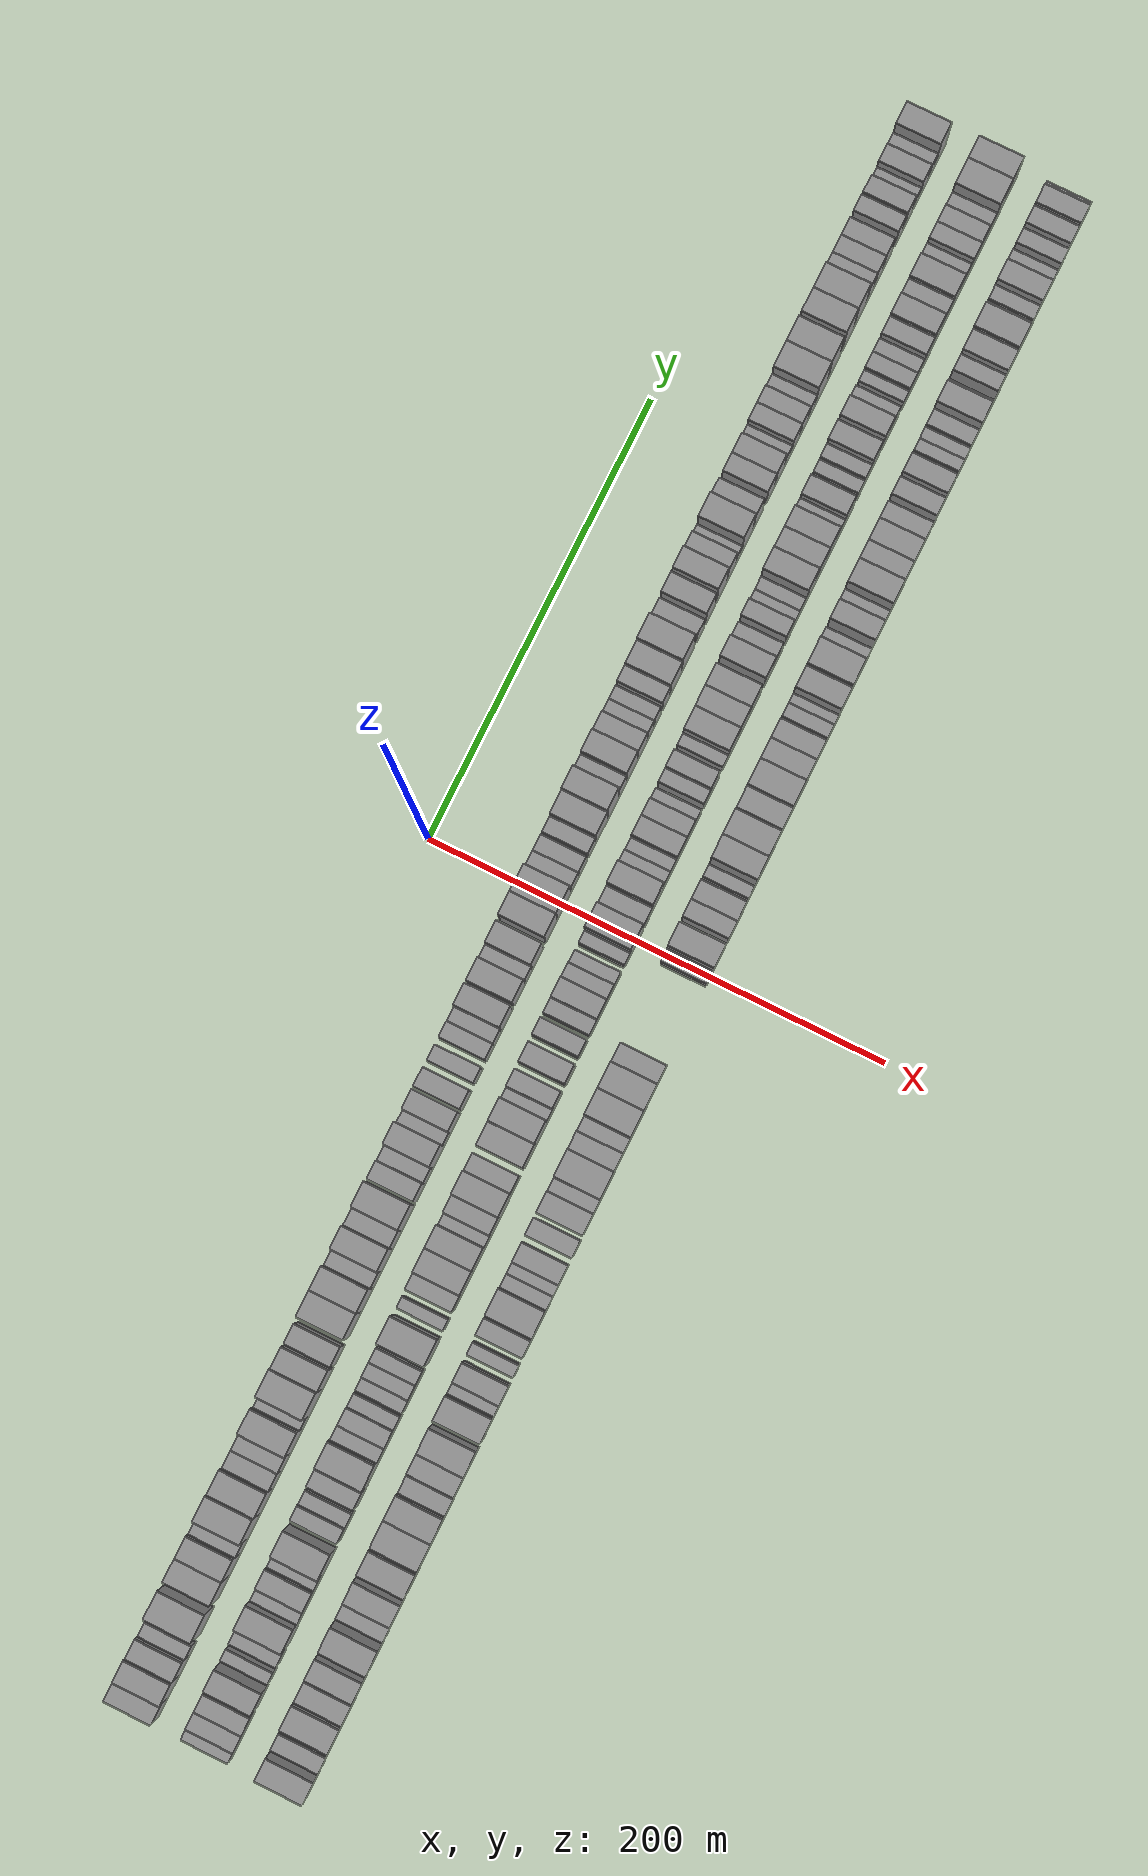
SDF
<sdf version="1.6">
 <world name="default">
  <scene>
   <sky><clouds><speed>12</speed></clouds></sky>
   <ambient>0.4 0.4 0.4 1</ambient>
   <background>0.7 0.7 0.7 1</background>
   <shadows>1</shadows>
  </scene>
  <gravity>0 0 -9.8066</gravity>
  <magnetic_field>6e-06 2.3e-05 -4.2e-05</magnetic_field>
  <physics default="0" name="default_physics" type="ode">
   <ode>
    <solver>
     <type>quick</type>
     <iters>10</iters>
     <sor>1.0</sor>
     <use_dynamic_moi_rescaling>0</use_dynamic_moi_rescaling>
    </solver>
    <constraints>
     <cfm>0</cfm>
     <erp>0.2</erp>
     <contact_max_correcting_vel>100</contact_max_correcting_vel>
     <contact_surface_layer>0.001</contact_surface_layer>
    </constraints>
   </ode>
   <max_step_size>0.004</max_step_size>
   <real_time_factor>1</real_time_factor>
   <real_time_update_rate>250</real_time_update_rate>
  </physics>
  <light name="sun" type="directional">
   <pose>0 0 10 0 0 0</pose>
   <diffuse>0.8 0.8 0.8 1</diffuse>
   <specular>0.2 0.2 0.2 1</specular>
   <attenuation>
    <range>1000</range>
    <constant>0.9</constant>
    <linear>0.01</linear>
    <quadratic>0.001</quadratic>
   </attenuation>
   <direction>-0.5 0.1 -0.9</direction>
  </light>
  <model name="building_1">
   <static>1</static>
   <pose>50.0000 -342.8980 0 0.000000 0.000000 0.000000</pose>
   <link name="link">
    <pose>0 0 9.00 0 0 0</pose>
    <collision name="collision"><geometry><box><size>20.0000 8.2040 18.0000</size></box></geometry></collision>
    <visual name="visual">
     <cast_shadows>0</cast_shadows>
     <geometry><box><size>20.0000 8.2040 18.0000</size></box></geometry>
     <material>
      <script>
       <uri>model://grey_wall/materials/scripts</uri>
       <uri>model://grey_wall/materials/textures</uri>
       <name>vrc/grey_wall</name>
      </script>
     </material>
    </visual>
   </link>
  </model>
  <model name="building_2">
   <static>1</static>
   <pose>50.0000 -334.2920 0 0.000000 0.000000 0.000000</pose>
   <link name="link">
    <pose>0 0 10.50 0 0 0</pose>
    <collision name="collision"><geometry><box><size>20.0000 9.0080 21.0000</size></box></geometry></collision>
    <visual name="visual">
     <cast_shadows>0</cast_shadows>
     <geometry><box><size>20.0000 9.0080 21.0000</size></box></geometry>
     <material>
      <script>
       <uri>model://grey_wall/materials/scripts</uri>
       <uri>model://grey_wall/materials/textures</uri>
       <name>vrc/grey_wall</name>
      </script>
     </material>
    </visual>
   </link>
  </model>
  <model name="building_3">
   <static>1</static>
   <pose>50.0000 -325.6805 0 0.000000 0.000000 0.000000</pose>
   <link name="link">
    <pose>0 0 9.00 0 0 0</pose>
    <collision name="collision"><geometry><box><size>20.0000 8.2150 18.0000</size></box></geometry></collision>
    <visual name="visual">
     <cast_shadows>0</cast_shadows>
     <geometry><box><size>20.0000 8.2150 18.0000</size></box></geometry>
     <material>
      <script>
       <uri>model://grey_wall/materials/scripts</uri>
       <uri>model://grey_wall/materials/textures</uri>
       <name>vrc/grey_wall</name>
      </script>
     </material>
    </visual>
   </link>
  </model>
  <model name="building_4">
   <static>1</static>
   <pose>50.0000 -318.6724 0 0.000000 0.000000 0.000000</pose>
   <link name="link">
    <pose>0 0 6.00 0 0 0</pose>
    <collision name="collision"><geometry><box><size>20.0000 5.8012 12.0000</size></box></geometry></collision>
    <visual name="visual">
     <cast_shadows>0</cast_shadows>
     <geometry><box><size>20.0000 5.8012 12.0000</size></box></geometry>
     <material>
      <script>
       <uri>model://grey_wall/materials/scripts</uri>
       <uri>model://grey_wall/materials/textures</uri>
       <name>vrc/grey_wall</name>
      </script>
     </material>
    </visual>
   </link>
  </model>
  <model name="building_5">
   <static>1</static>
   <pose>50.0000 -306.9197 0 0.000000 0.000000 0.000000</pose>
   <link name="link">
    <pose>0 0 12.00 0 0 0</pose>
    <collision name="collision"><geometry><box><size>20.0000 11.7041 24.0000</size></box></geometry></collision>
    <visual name="visual">
     <cast_shadows>0</cast_shadows>
     <geometry><box><size>20.0000 11.7041 24.0000</size></box></geometry>
     <material>
      <script>
       <uri>model://grey_wall/materials/scripts</uri>
       <uri>model://grey_wall/materials/textures</uri>
       <name>vrc/grey_wall</name>
      </script>
     </material>
    </visual>
   </link>
  </model>
  <model name="building_6">
   <static>1</static>
   <pose>50.0000 -293.1795 0 0.000000 0.000000 0.000000</pose>
   <link name="link">
    <pose>0 0 10.50 0 0 0</pose>
    <collision name="collision"><geometry><box><size>20.0000 9.7764 21.0000</size></box></geometry></collision>
    <visual name="visual">
     <cast_shadows>0</cast_shadows>
     <geometry><box><size>20.0000 9.7764 21.0000</size></box></geometry>
     <material>
      <script>
       <uri>model://grey_wall/materials/scripts</uri>
       <uri>model://grey_wall/materials/textures</uri>
       <name>vrc/grey_wall</name>
      </script>
     </material>
    </visual>
   </link>
  </model>
  <model name="building_7">
   <static>1</static>
   <pose>50.0000 -283.6696 0 0.000000 0.000000 0.000000</pose>
   <link name="link">
    <pose>0 0 10.50 0 0 0</pose>
    <collision name="collision"><geometry><box><size>20.0000 9.2435 21.0000</size></box></geometry></collision>
    <visual name="visual">
     <cast_shadows>0</cast_shadows>
     <geometry><box><size>20.0000 9.2435 21.0000</size></box></geometry>
     <material>
      <script>
       <uri>model://grey_wall/materials/scripts</uri>
       <uri>model://grey_wall/materials/textures</uri>
       <name>vrc/grey_wall</name>
      </script>
     </material>
    </visual>
   </link>
  </model>
  <model name="building_8">
   <static>1</static>
   <pose>50.0000 -275.9182 0 0.000000 0.000000 0.000000</pose>
   <link name="link">
    <pose>0 0 7.50 0 0 0</pose>
    <collision name="collision"><geometry><box><size>20.0000 6.2592 15.0000</size></box></geometry></collision>
    <visual name="visual">
     <cast_shadows>0</cast_shadows>
     <geometry><box><size>20.0000 6.2592 15.0000</size></box></geometry>
     <material>
      <script>
       <uri>model://grey_wall/materials/scripts</uri>
       <uri>model://grey_wall/materials/textures</uri>
       <name>vrc/grey_wall</name>
      </script>
     </material>
    </visual>
   </link>
  </model>
  <model name="building_9">
   <static>1</static>
   <pose>50.0000 -267.4765 0 0.000000 0.000000 0.000000</pose>
   <link name="link">
    <pose>0 0 12.00 0 0 0</pose>
    <collision name="collision"><geometry><box><size>20.0000 10.6244 24.0000</size></box></geometry></collision>
    <visual name="visual">
     <cast_shadows>0</cast_shadows>
     <geometry><box><size>20.0000 10.6244 24.0000</size></box></geometry>
     <material>
      <script>
       <uri>model://grey_wall/materials/scripts</uri>
       <uri>model://grey_wall/materials/textures</uri>
       <name>vrc/grey_wall</name>
      </script>
     </material>
    </visual>
   </link>
  </model>
  <model name="building_10">
   <static>1</static>
   <pose>50.0000 -256.9345 0 0.000000 0.000000 0.000000</pose>
   <link name="link">
    <pose>0 0 10.50 0 0 0</pose>
    <collision name="collision"><geometry><box><size>20.0000 10.4595 21.0000</size></box></geometry></collision>
    <visual name="visual">
     <cast_shadows>0</cast_shadows>
     <geometry><box><size>20.0000 10.4595 21.0000</size></box></geometry>
     <material>
      <script>
       <uri>model://grey_wall/materials/scripts</uri>
       <uri>model://grey_wall/materials/textures</uri>
       <name>vrc/grey_wall</name>
      </script>
     </material>
    </visual>
   </link>
  </model>
  <model name="building_11">
   <static>1</static>
   <pose>50.0000 -247.9561 0 0.000000 0.000000 0.000000</pose>
   <link name="link">
    <pose>0 0 7.50 0 0 0</pose>
    <collision name="collision"><geometry><box><size>20.0000 7.4973 15.0000</size></box></geometry></collision>
    <visual name="visual">
     <cast_shadows>0</cast_shadows>
     <geometry><box><size>20.0000 7.4973 15.0000</size></box></geometry>
     <material>
      <script>
       <uri>model://grey_wall/materials/scripts</uri>
       <uri>model://grey_wall/materials/textures</uri>
       <name>vrc/grey_wall</name>
      </script>
     </material>
    </visual>
   </link>
  </model>
  <model name="building_12">
   <static>1</static>
   <pose>50.0000 -240.6093 0 0.000000 0.000000 0.000000</pose>
   <link name="link">
    <pose>0 0 7.50 0 0 0</pose>
    <collision name="collision"><geometry><box><size>20.0000 7.1963 15.0000</size></box></geometry></collision>
    <visual name="visual">
     <cast_shadows>0</cast_shadows>
     <geometry><box><size>20.0000 7.1963 15.0000</size></box></geometry>
     <material>
      <script>
       <uri>model://grey_wall/materials/scripts</uri>
       <uri>model://grey_wall/materials/textures</uri>
       <name>vrc/grey_wall</name>
      </script>
     </material>
    </visual>
   </link>
  </model>
  <model name="building_13">
   <static>1</static>
   <pose>50.0000 -231.7747 0 0.000000 0.000000 0.000000</pose>
   <link name="link">
    <pose>0 0 10.50 0 0 0</pose>
    <collision name="collision"><geometry><box><size>20.0000 10.4729 21.0000</size></box></geometry></collision>
    <visual name="visual">
     <cast_shadows>0</cast_shadows>
     <geometry><box><size>20.0000 10.4729 21.0000</size></box></geometry>
     <material>
      <script>
       <uri>model://grey_wall/materials/scripts</uri>
       <uri>model://grey_wall/materials/textures</uri>
       <name>vrc/grey_wall</name>
      </script>
     </material>
    </visual>
   </link>
  </model>
  <model name="building_14">
   <static>1</static>
   <pose>50.0000 -223.9534 0 0.000000 0.000000 0.000000</pose>
   <link name="link">
    <pose>0 0 6.00 0 0 0</pose>
    <collision name="collision"><geometry><box><size>20.0000 5.1696 12.0000</size></box></geometry></collision>
    <visual name="visual">
     <cast_shadows>0</cast_shadows>
     <geometry><box><size>20.0000 5.1696 12.0000</size></box></geometry>
     <material>
      <script>
       <uri>model://grey_wall/materials/scripts</uri>
       <uri>model://grey_wall/materials/textures</uri>
       <name>vrc/grey_wall</name>
      </script>
     </material>
    </visual>
   </link>
  </model>
  <model name="building_15">
   <static>1</static>
   <pose>50.0000 -215.5958 0 0.000000 0.000000 0.000000</pose>
   <link name="link">
    <pose>0 0 12.00 0 0 0</pose>
    <collision name="collision"><geometry><box><size>20.0000 11.5456 24.0000</size></box></geometry></collision>
    <visual name="visual">
     <cast_shadows>0</cast_shadows>
     <geometry><box><size>20.0000 11.5456 24.0000</size></box></geometry>
     <material>
      <script>
       <uri>model://grey_wall/materials/scripts</uri>
       <uri>model://grey_wall/materials/textures</uri>
       <name>vrc/grey_wall</name>
      </script>
     </material>
    </visual>
   </link>
  </model>
  <model name="building_16">
   <static>1</static>
   <pose>50.0000 -205.1998 0 0.000000 0.000000 0.000000</pose>
   <link name="link">
    <pose>0 0 10.50 0 0 0</pose>
    <collision name="collision"><geometry><box><size>20.0000 9.2464 21.0000</size></box></geometry></collision>
    <visual name="visual">
     <cast_shadows>0</cast_shadows>
     <geometry><box><size>20.0000 9.2464 21.0000</size></box></geometry>
     <material>
      <script>
       <uri>model://grey_wall/materials/scripts</uri>
       <uri>model://grey_wall/materials/textures</uri>
       <name>vrc/grey_wall</name>
      </script>
     </material>
    </visual>
   </link>
  </model>
  <model name="building_17">
   <static>1</static>
   <pose>50.0000 -195.2882 0 0.000000 0.000000 0.000000</pose>
   <link name="link">
    <pose>0 0 9.00 0 0 0</pose>
    <collision name="collision"><geometry><box><size>20.0000 8.5769 18.0000</size></box></geometry></collision>
    <visual name="visual">
     <cast_shadows>0</cast_shadows>
     <geometry><box><size>20.0000 8.5769 18.0000</size></box></geometry>
     <material>
      <script>
       <uri>model://grey_wall/materials/scripts</uri>
       <uri>model://grey_wall/materials/textures</uri>
       <name>vrc/grey_wall</name>
      </script>
     </material>
    </visual>
   </link>
  </model>
  <model name="building_18">
   <static>1</static>
   <pose>50.0000 -182.4111 0 0.000000 0.000000 0.000000</pose>
   <link name="link">
    <pose>0 0 12.00 0 0 0</pose>
    <collision name="collision"><geometry><box><size>20.0000 11.1772 24.0000</size></box></geometry></collision>
    <visual name="visual">
     <cast_shadows>0</cast_shadows>
     <geometry><box><size>20.0000 11.1772 24.0000</size></box></geometry>
     <material>
      <script>
       <uri>model://grey_wall/materials/scripts</uri>
       <uri>model://grey_wall/materials/textures</uri>
       <name>vrc/grey_wall</name>
      </script>
     </material>
    </visual>
   </link>
  </model>
  <model name="building_19">
   <static>1</static>
   <pose>50.0000 -171.7365 0 0.000000 0.000000 0.000000</pose>
   <link name="link">
    <pose>0 0 12.00 0 0 0</pose>
    <collision name="collision"><geometry><box><size>20.0000 10.1720 24.0000</size></box></geometry></collision>
    <visual name="visual">
     <cast_shadows>0</cast_shadows>
     <geometry><box><size>20.0000 10.1720 24.0000</size></box></geometry>
     <material>
      <script>
       <uri>model://grey_wall/materials/scripts</uri>
       <uri>model://grey_wall/materials/textures</uri>
       <name>vrc/grey_wall</name>
      </script>
     </material>
    </visual>
   </link>
  </model>
  <model name="building_20">
   <static>1</static>
   <pose>50.0000 -163.0944 0 0.000000 0.000000 0.000000</pose>
   <link name="link">
    <pose>0 0 7.50 0 0 0</pose>
    <collision name="collision"><geometry><box><size>20.0000 7.1122 15.0000</size></box></geometry></collision>
    <visual name="visual">
     <cast_shadows>0</cast_shadows>
     <geometry><box><size>20.0000 7.1122 15.0000</size></box></geometry>
     <material>
      <script>
       <uri>model://grey_wall/materials/scripts</uri>
       <uri>model://grey_wall/materials/textures</uri>
       <name>vrc/grey_wall</name>
      </script>
     </material>
    </visual>
   </link>
  </model>
  <model name="building_21">
   <static>1</static>
   <pose>50.0000 -154.5888 0 0.000000 0.000000 0.000000</pose>
   <link name="link">
    <pose>0 0 12.00 0 0 0</pose>
    <collision name="collision"><geometry><box><size>20.0000 9.8990 24.0000</size></box></geometry></collision>
    <visual name="visual">
     <cast_shadows>0</cast_shadows>
     <geometry><box><size>20.0000 9.8990 24.0000</size></box></geometry>
     <material>
      <script>
       <uri>model://grey_wall/materials/scripts</uri>
       <uri>model://grey_wall/materials/textures</uri>
       <name>vrc/grey_wall</name>
      </script>
     </material>
    </visual>
   </link>
  </model>
  <model name="building_22">
   <static>1</static>
   <pose>50.0000 -145.7446 0 0.000000 0.000000 0.000000</pose>
   <link name="link">
    <pose>0 0 9.00 0 0 0</pose>
    <collision name="collision"><geometry><box><size>20.0000 7.7892 18.0000</size></box></geometry></collision>
    <visual name="visual">
     <cast_shadows>0</cast_shadows>
     <geometry><box><size>20.0000 7.7892 18.0000</size></box></geometry>
     <material>
      <script>
       <uri>model://grey_wall/materials/scripts</uri>
       <uri>model://grey_wall/materials/textures</uri>
       <name>vrc/grey_wall</name>
      </script>
     </material>
    </visual>
   </link>
  </model>
  <model name="building_23">
   <static>1</static>
   <pose>50.0000 -136.4296 0 0.000000 0.000000 0.000000</pose>
   <link name="link">
    <pose>0 0 12.00 0 0 0</pose>
    <collision name="collision"><geometry><box><size>20.0000 10.8409 24.0000</size></box></geometry></collision>
    <visual name="visual">
     <cast_shadows>0</cast_shadows>
     <geometry><box><size>20.0000 10.8409 24.0000</size></box></geometry>
     <material>
      <script>
       <uri>model://grey_wall/materials/scripts</uri>
       <uri>model://grey_wall/materials/textures</uri>
       <name>vrc/grey_wall</name>
      </script>
     </material>
    </visual>
   </link>
  </model>
  <model name="building_24">
   <static>1</static>
   <pose>50.0000 -125.9622 0 0.000000 0.000000 0.000000</pose>
   <link name="link">
    <pose>0 0 9.00 0 0 0</pose>
    <collision name="collision"><geometry><box><size>20.0000 8.0939 18.0000</size></box></geometry></collision>
    <visual name="visual">
     <cast_shadows>0</cast_shadows>
     <geometry><box><size>20.0000 8.0939 18.0000</size></box></geometry>
     <material>
      <script>
       <uri>model://grey_wall/materials/scripts</uri>
       <uri>model://grey_wall/materials/textures</uri>
       <name>vrc/grey_wall</name>
      </script>
     </material>
    </visual>
   </link>
  </model>
  <model name="building_25">
   <static>1</static>
   <pose>50.0000 -118.5604 0 0.000000 0.000000 0.000000</pose>
   <link name="link">
    <pose>0 0 7.50 0 0 0</pose>
    <collision name="collision"><geometry><box><size>20.0000 6.7097 15.0000</size></box></geometry></collision>
    <visual name="visual">
     <cast_shadows>0</cast_shadows>
     <geometry><box><size>20.0000 6.7097 15.0000</size></box></geometry>
     <material>
      <script>
       <uri>model://grey_wall/materials/scripts</uri>
       <uri>model://grey_wall/materials/textures</uri>
       <name>vrc/grey_wall</name>
      </script>
     </material>
    </visual>
   </link>
  </model>
  <model name="building_26">
   <static>1</static>
   <pose>50.0000 -110.4016 0 0.000000 0.000000 0.000000</pose>
   <link name="link">
    <pose>0 0 12.00 0 0 0</pose>
    <collision name="collision"><geometry><box><size>20.0000 9.6079 24.0000</size></box></geometry></collision>
    <visual name="visual">
     <cast_shadows>0</cast_shadows>
     <geometry><box><size>20.0000 9.6079 24.0000</size></box></geometry>
     <material>
      <script>
       <uri>model://grey_wall/materials/scripts</uri>
       <uri>model://grey_wall/materials/textures</uri>
       <name>vrc/grey_wall</name>
      </script>
     </material>
    </visual>
   </link>
  </model>
  <model name="building_27">
   <static>1</static>
   <pose>50.0000 -102.8673 0 0.000000 0.000000 0.000000</pose>
   <link name="link">
    <pose>0 0 6.00 0 0 0</pose>
    <collision name="collision"><geometry><box><size>20.0000 5.4606 12.0000</size></box></geometry></collision>
    <visual name="visual">
     <cast_shadows>0</cast_shadows>
     <geometry><box><size>20.0000 5.4606 12.0000</size></box></geometry>
     <material>
      <script>
       <uri>model://grey_wall/materials/scripts</uri>
       <uri>model://grey_wall/materials/textures</uri>
       <name>vrc/grey_wall</name>
      </script>
     </material>
    </visual>
   </link>
  </model>
  <model name="building_28">
   <static>1</static>
   <pose>50.0000 -95.7988 0 0.000000 0.000000 0.000000</pose>
   <link name="link">
    <pose>0 0 9.00 0 0 0</pose>
    <collision name="collision"><geometry><box><size>20.0000 8.6765 18.0000</size></box></geometry></collision>
    <visual name="visual">
     <cast_shadows>0</cast_shadows>
     <geometry><box><size>20.0000 8.6765 18.0000</size></box></geometry>
     <material>
      <script>
       <uri>model://grey_wall/materials/scripts</uri>
       <uri>model://grey_wall/materials/textures</uri>
       <name>vrc/grey_wall</name>
      </script>
     </material>
    </visual>
   </link>
  </model>
  <model name="building_29">
   <static>1</static>
   <pose>50.0000 -86.2173 0 0.000000 0.000000 0.000000</pose>
   <link name="link">
    <pose>0 0 9.00 0 0 0</pose>
    <collision name="collision"><geometry><box><size>20.0000 8.4864 18.0000</size></box></geometry></collision>
    <visual name="visual">
     <cast_shadows>0</cast_shadows>
     <geometry><box><size>20.0000 8.4864 18.0000</size></box></geometry>
     <material>
      <script>
       <uri>model://grey_wall/materials/scripts</uri>
       <uri>model://grey_wall/materials/textures</uri>
       <name>vrc/grey_wall</name>
      </script>
     </material>
    </visual>
   </link>
  </model>
  <model name="building_30">
   <static>1</static>
   <pose>50.0000 -75.5084 0 0.000000 0.000000 0.000000</pose>
   <link name="link">
    <pose>0 0 7.50 0 0 0</pose>
    <collision name="collision"><geometry><box><size>20.0000 6.9314 15.0000</size></box></geometry></collision>
    <visual name="visual">
     <cast_shadows>0</cast_shadows>
     <geometry><box><size>20.0000 6.9314 15.0000</size></box></geometry>
     <material>
      <script>
       <uri>model://grey_wall/materials/scripts</uri>
       <uri>model://grey_wall/materials/textures</uri>
       <name>vrc/grey_wall</name>
      </script>
     </material>
    </visual>
   </link>
  </model>
  <model name="building_31">
   <static>1</static>
   <pose>50.0000 -65.5238 0 0.000000 0.000000 0.000000</pose>
   <link name="link">
    <pose>0 0 7.50 0 0 0</pose>
    <collision name="collision"><geometry><box><size>20.0000 7.0378 15.0000</size></box></geometry></collision>
    <visual name="visual">
     <cast_shadows>0</cast_shadows>
     <geometry><box><size>20.0000 7.0378 15.0000</size></box></geometry>
     <material>
      <script>
       <uri>model://grey_wall/materials/scripts</uri>
       <uri>model://grey_wall/materials/textures</uri>
       <name>vrc/grey_wall</name>
      </script>
     </material>
    </visual>
   </link>
  </model>
  <model name="building_32">
   <static>1</static>
   <pose>50.0000 -58.8244 0 0.000000 0.000000 0.000000</pose>
   <link name="link">
    <pose>0 0 7.50 0 0 0</pose>
    <collision name="collision"><geometry><box><size>20.0000 6.3609 15.0000</size></box></geometry></collision>
    <visual name="visual">
     <cast_shadows>0</cast_shadows>
     <geometry><box><size>20.0000 6.3609 15.0000</size></box></geometry>
     <material>
      <script>
       <uri>model://grey_wall/materials/scripts</uri>
       <uri>model://grey_wall/materials/textures</uri>
       <name>vrc/grey_wall</name>
      </script>
     </material>
    </visual>
   </link>
  </model>
  <model name="building_33">
   <static>1</static>
   <pose>50.0000 -50.7950 0 0.000000 0.000000 0.000000</pose>
   <link name="link">
    <pose>0 0 10.50 0 0 0</pose>
    <collision name="collision"><geometry><box><size>20.0000 9.6981 21.0000</size></box></geometry></collision>
    <visual name="visual">
     <cast_shadows>0</cast_shadows>
     <geometry><box><size>20.0000 9.6981 21.0000</size></box></geometry>
     <material>
      <script>
       <uri>model://grey_wall/materials/scripts</uri>
       <uri>model://grey_wall/materials/textures</uri>
       <name>vrc/grey_wall</name>
      </script>
     </material>
    </visual>
   </link>
  </model>
  <model name="building_34">
   <static>1</static>
   <pose>50.0000 -39.8899 0 0.000000 0.000000 0.000000</pose>
   <link name="link">
    <pose>0 0 10.50 0 0 0</pose>
    <collision name="collision"><geometry><box><size>20.0000 10.1120 21.0000</size></box></geometry></collision>
    <visual name="visual">
     <cast_shadows>0</cast_shadows>
     <geometry><box><size>20.0000 10.1120 21.0000</size></box></geometry>
     <material>
      <script>
       <uri>model://grey_wall/materials/scripts</uri>
       <uri>model://grey_wall/materials/textures</uri>
       <name>vrc/grey_wall</name>
      </script>
     </material>
    </visual>
   </link>
  </model>
  <model name="building_35">
   <static>1</static>
   <pose>50.0000 -31.7334 0 0.000000 0.000000 0.000000</pose>
   <link name="link">
    <pose>0 0 7.50 0 0 0</pose>
    <collision name="collision"><geometry><box><size>20.0000 6.2009 15.0000</size></box></geometry></collision>
    <visual name="visual">
     <cast_shadows>0</cast_shadows>
     <geometry><box><size>20.0000 6.2009 15.0000</size></box></geometry>
     <material>
      <script>
       <uri>model://grey_wall/materials/scripts</uri>
       <uri>model://grey_wall/materials/textures</uri>
       <name>vrc/grey_wall</name>
      </script>
     </material>
    </visual>
   </link>
  </model>
  <model name="building_36">
   <static>1</static>
   <pose>50.0000 -23.7923 0 0.000000 0.000000 0.000000</pose>
   <link name="link">
    <pose>0 0 10.50 0 0 0</pose>
    <collision name="collision"><geometry><box><size>20.0000 9.6813 21.0000</size></box></geometry></collision>
    <visual name="visual">
     <cast_shadows>0</cast_shadows>
     <geometry><box><size>20.0000 9.6813 21.0000</size></box></geometry>
     <material>
      <script>
       <uri>model://grey_wall/materials/scripts</uri>
       <uri>model://grey_wall/materials/textures</uri>
       <name>vrc/grey_wall</name>
      </script>
     </material>
    </visual>
   </link>
  </model>
  <model name="building_37">
   <static>1</static>
   <pose>50.0000 -11.8276 0 0.000000 0.000000 0.000000</pose>
   <link name="link">
    <pose>0 0 12.00 0 0 0</pose>
    <collision name="collision"><geometry><box><size>20.0000 10.2482 24.0000</size></box></geometry></collision>
    <visual name="visual">
     <cast_shadows>0</cast_shadows>
     <geometry><box><size>20.0000 10.2482 24.0000</size></box></geometry>
     <material>
      <script>
       <uri>model://grey_wall/materials/scripts</uri>
       <uri>model://grey_wall/materials/textures</uri>
       <name>vrc/grey_wall</name>
      </script>
     </material>
    </visual>
   </link>
  </model>
  <model name="building_38">
   <static>1</static>
   <pose>50.0000 -0.7172 0 0.000000 0.000000 0.000000</pose>
   <link name="link">
    <pose>0 0 12.00 0 0 0</pose>
    <collision name="collision"><geometry><box><size>20.0000 11.9725 24.0000</size></box></geometry></collision>
    <visual name="visual">
     <cast_shadows>0</cast_shadows>
     <geometry><box><size>20.0000 11.9725 24.0000</size></box></geometry>
     <material>
      <script>
       <uri>model://grey_wall/materials/scripts</uri>
       <uri>model://grey_wall/materials/textures</uri>
       <name>vrc/grey_wall</name>
      </script>
     </material>
    </visual>
   </link>
  </model>
  <model name="building_39">
   <static>1</static>
   <pose>50.0000 8.8545 0 0.000000 0.000000 0.000000</pose>
   <link name="link">
    <pose>0 0 7.50 0 0 0</pose>
    <collision name="collision"><geometry><box><size>20.0000 7.1708 15.0000</size></box></geometry></collision>
    <visual name="visual">
     <cast_shadows>0</cast_shadows>
     <geometry><box><size>20.0000 7.1708 15.0000</size></box></geometry>
     <material>
      <script>
       <uri>model://grey_wall/materials/scripts</uri>
       <uri>model://grey_wall/materials/textures</uri>
       <name>vrc/grey_wall</name>
      </script>
     </material>
    </visual>
   </link>
  </model>
  <model name="building_40">
   <static>1</static>
   <pose>50.0000 15.9786 0 0.000000 0.000000 0.000000</pose>
   <link name="link">
    <pose>0 0 7.50 0 0 0</pose>
    <collision name="collision"><geometry><box><size>20.0000 7.0775 15.0000</size></box></geometry></collision>
    <visual name="visual">
     <cast_shadows>0</cast_shadows>
     <geometry><box><size>20.0000 7.0775 15.0000</size></box></geometry>
     <material>
      <script>
       <uri>model://grey_wall/materials/scripts</uri>
       <uri>model://grey_wall/materials/textures</uri>
       <name>vrc/grey_wall</name>
      </script>
     </material>
    </visual>
   </link>
  </model>
  <model name="building_41">
   <static>1</static>
   <pose>50.0000 24.0389 0 0.000000 0.000000 0.000000</pose>
   <link name="link">
    <pose>0 0 7.50 0 0 0</pose>
    <collision name="collision"><geometry><box><size>20.0000 7.0430 15.0000</size></box></geometry></collision>
    <visual name="visual">
     <cast_shadows>0</cast_shadows>
     <geometry><box><size>20.0000 7.0430 15.0000</size></box></geometry>
     <material>
      <script>
       <uri>model://grey_wall/materials/scripts</uri>
       <uri>model://grey_wall/materials/textures</uri>
       <name>vrc/grey_wall</name>
      </script>
     </material>
    </visual>
   </link>
  </model>
  <model name="building_42">
   <static>1</static>
   <pose>50.0000 32.7854 0 0.000000 0.000000 0.000000</pose>
   <link name="link">
    <pose>0 0 10.50 0 0 0</pose>
    <collision name="collision"><geometry><box><size>20.0000 10.4501 21.0000</size></box></geometry></collision>
    <visual name="visual">
     <cast_shadows>0</cast_shadows>
     <geometry><box><size>20.0000 10.4501 21.0000</size></box></geometry>
     <material>
      <script>
       <uri>model://grey_wall/materials/scripts</uri>
       <uri>model://grey_wall/materials/textures</uri>
       <name>vrc/grey_wall</name>
      </script>
     </material>
    </visual>
   </link>
  </model>
  <model name="building_43">
   <static>1</static>
   <pose>50.0000 43.0834 0 0.000000 0.000000 0.000000</pose>
   <link name="link">
    <pose>0 0 12.00 0 0 0</pose>
    <collision name="collision"><geometry><box><size>20.0000 10.1457 24.0000</size></box></geometry></collision>
    <visual name="visual">
     <cast_shadows>0</cast_shadows>
     <geometry><box><size>20.0000 10.1457 24.0000</size></box></geometry>
     <material>
      <script>
       <uri>model://grey_wall/materials/scripts</uri>
       <uri>model://grey_wall/materials/textures</uri>
       <name>vrc/grey_wall</name>
      </script>
     </material>
    </visual>
   </link>
  </model>
  <model name="building_44">
   <static>1</static>
   <pose>50.0000 51.5074 0 0.000000 0.000000 0.000000</pose>
   <link name="link">
    <pose>0 0 7.50 0 0 0</pose>
    <collision name="collision"><geometry><box><size>20.0000 6.7023 15.0000</size></box></geometry></collision>
    <visual name="visual">
     <cast_shadows>0</cast_shadows>
     <geometry><box><size>20.0000 6.7023 15.0000</size></box></geometry>
     <material>
      <script>
       <uri>model://grey_wall/materials/scripts</uri>
       <uri>model://grey_wall/materials/textures</uri>
       <name>vrc/grey_wall</name>
      </script>
     </material>
    </visual>
   </link>
  </model>
  <model name="building_45">
   <static>1</static>
   <pose>50.0000 59.8590 0 0.000000 0.000000 0.000000</pose>
   <link name="link">
    <pose>0 0 10.50 0 0 0</pose>
    <collision name="collision"><geometry><box><size>20.0000 10.0010 21.0000</size></box></geometry></collision>
    <visual name="visual">
     <cast_shadows>0</cast_shadows>
     <geometry><box><size>20.0000 10.0010 21.0000</size></box></geometry>
     <material>
      <script>
       <uri>model://grey_wall/materials/scripts</uri>
       <uri>model://grey_wall/materials/textures</uri>
       <name>vrc/grey_wall</name>
      </script>
     </material>
    </visual>
   </link>
  </model>
  <model name="building_46">
   <static>1</static>
   <pose>50.0000 69.1309 0 0.000000 0.000000 0.000000</pose>
   <link name="link">
    <pose>0 0 9.00 0 0 0</pose>
    <collision name="collision"><geometry><box><size>20.0000 8.5427 18.0000</size></box></geometry></collision>
    <visual name="visual">
     <cast_shadows>0</cast_shadows>
     <geometry><box><size>20.0000 8.5427 18.0000</size></box></geometry>
     <material>
      <script>
       <uri>model://grey_wall/materials/scripts</uri>
       <uri>model://grey_wall/materials/textures</uri>
       <name>vrc/grey_wall</name>
      </script>
     </material>
    </visual>
   </link>
  </model>
  <model name="building_47">
   <static>1</static>
   <pose>50.0000 76.4442 0 0.000000 0.000000 0.000000</pose>
   <link name="link">
    <pose>0 0 7.50 0 0 0</pose>
    <collision name="collision"><geometry><box><size>20.0000 6.0840 15.0000</size></box></geometry></collision>
    <visual name="visual">
     <cast_shadows>0</cast_shadows>
     <geometry><box><size>20.0000 6.0840 15.0000</size></box></geometry>
     <material>
      <script>
       <uri>model://grey_wall/materials/scripts</uri>
       <uri>model://grey_wall/materials/textures</uri>
       <name>vrc/grey_wall</name>
      </script>
     </material>
    </visual>
   </link>
  </model>
  <model name="building_48">
   <static>1</static>
   <pose>50.0000 82.5288 0 0.000000 0.000000 0.000000</pose>
   <link name="link">
    <pose>0 0 7.50 0 0 0</pose>
    <collision name="collision"><geometry><box><size>20.0000 6.0853 15.0000</size></box></geometry></collision>
    <visual name="visual">
     <cast_shadows>0</cast_shadows>
     <geometry><box><size>20.0000 6.0853 15.0000</size></box></geometry>
     <material>
      <script>
       <uri>model://grey_wall/materials/scripts</uri>
       <uri>model://grey_wall/materials/textures</uri>
       <name>vrc/grey_wall</name>
      </script>
     </material>
    </visual>
   </link>
  </model>
  <model name="building_49">
   <static>1</static>
   <pose>50.0000 90.2138 0 0.000000 0.000000 0.000000</pose>
   <link name="link">
    <pose>0 0 9.00 0 0 0</pose>
    <collision name="collision"><geometry><box><size>20.0000 7.2847 18.0000</size></box></geometry></collision>
    <visual name="visual">
     <cast_shadows>0</cast_shadows>
     <geometry><box><size>20.0000 7.2847 18.0000</size></box></geometry>
     <material>
      <script>
       <uri>model://grey_wall/materials/scripts</uri>
       <uri>model://grey_wall/materials/textures</uri>
       <name>vrc/grey_wall</name>
      </script>
     </material>
    </visual>
   </link>
  </model>
  <model name="building_50">
   <static>1</static>
   <pose>50.0000 99.0568 0 0.000000 0.000000 0.000000</pose>
   <link name="link">
    <pose>0 0 10.50 0 0 0</pose>
    <collision name="collision"><geometry><box><size>20.0000 10.4013 21.0000</size></box></geometry></collision>
    <visual name="visual">
     <cast_shadows>0</cast_shadows>
     <geometry><box><size>20.0000 10.4013 21.0000</size></box></geometry>
     <material>
      <script>
       <uri>model://grey_wall/materials/scripts</uri>
       <uri>model://grey_wall/materials/textures</uri>
       <name>vrc/grey_wall</name>
      </script>
     </material>
    </visual>
   </link>
  </model>
  <model name="building_51">
   <static>1</static>
   <pose>50.0000 109.9423 0 0.000000 0.000000 0.000000</pose>
   <link name="link">
    <pose>0 0 12.00 0 0 0</pose>
    <collision name="collision"><geometry><box><size>20.0000 11.3697 24.0000</size></box></geometry></collision>
    <visual name="visual">
     <cast_shadows>0</cast_shadows>
     <geometry><box><size>20.0000 11.3697 24.0000</size></box></geometry>
     <material>
      <script>
       <uri>model://grey_wall/materials/scripts</uri>
       <uri>model://grey_wall/materials/textures</uri>
       <name>vrc/grey_wall</name>
      </script>
     </material>
    </visual>
   </link>
  </model>
  <model name="building_52">
   <static>1</static>
   <pose>50.0000 121.1510 0 0.000000 0.000000 0.000000</pose>
   <link name="link">
    <pose>0 0 7.50 0 0 0</pose>
    <collision name="collision"><geometry><box><size>20.0000 7.0476 15.0000</size></box></geometry></collision>
    <visual name="visual">
     <cast_shadows>0</cast_shadows>
     <geometry><box><size>20.0000 7.0476 15.0000</size></box></geometry>
     <material>
      <script>
       <uri>model://grey_wall/materials/scripts</uri>
       <uri>model://grey_wall/materials/textures</uri>
       <name>vrc/grey_wall</name>
      </script>
     </material>
    </visual>
   </link>
  </model>
  <model name="building_53">
   <static>1</static>
   <pose>50.0000 130.2038 0 0.000000 0.000000 0.000000</pose>
   <link name="link">
    <pose>0 0 10.50 0 0 0</pose>
    <collision name="collision"><geometry><box><size>20.0000 9.0579 21.0000</size></box></geometry></collision>
    <visual name="visual">
     <cast_shadows>0</cast_shadows>
     <geometry><box><size>20.0000 9.0579 21.0000</size></box></geometry>
     <material>
      <script>
       <uri>model://grey_wall/materials/scripts</uri>
       <uri>model://grey_wall/materials/textures</uri>
       <name>vrc/grey_wall</name>
      </script>
     </material>
    </visual>
   </link>
  </model>
  <model name="building_54">
   <static>1</static>
   <pose>50.0000 140.5833 0 0.000000 0.000000 0.000000</pose>
   <link name="link">
    <pose>0 0 12.00 0 0 0</pose>
    <collision name="collision"><geometry><box><size>20.0000 9.7012 24.0000</size></box></geometry></collision>
    <visual name="visual">
     <cast_shadows>0</cast_shadows>
     <geometry><box><size>20.0000 9.7012 24.0000</size></box></geometry>
     <material>
      <script>
       <uri>model://grey_wall/materials/scripts</uri>
       <uri>model://grey_wall/materials/textures</uri>
       <name>vrc/grey_wall</name>
      </script>
     </material>
    </visual>
   </link>
  </model>
  <model name="building_55">
   <static>1</static>
   <pose>50.0000 149.6270 0 0.000000 0.000000 0.000000</pose>
   <link name="link">
    <pose>0 0 9.00 0 0 0</pose>
    <collision name="collision"><geometry><box><size>20.0000 8.3863 18.0000</size></box></geometry></collision>
    <visual name="visual">
     <cast_shadows>0</cast_shadows>
     <geometry><box><size>20.0000 8.3863 18.0000</size></box></geometry>
     <material>
      <script>
       <uri>model://grey_wall/materials/scripts</uri>
       <uri>model://grey_wall/materials/textures</uri>
       <name>vrc/grey_wall</name>
      </script>
     </material>
    </visual>
   </link>
  </model>
  <model name="building_56">
   <static>1</static>
   <pose>50.0000 156.2234 0 0.000000 0.000000 0.000000</pose>
   <link name="link">
    <pose>0 0 6.00 0 0 0</pose>
    <collision name="collision"><geometry><box><size>20.0000 4.8064 12.0000</size></box></geometry></collision>
    <visual name="visual">
     <cast_shadows>0</cast_shadows>
     <geometry><box><size>20.0000 4.8064 12.0000</size></box></geometry>
     <material>
      <script>
       <uri>model://grey_wall/materials/scripts</uri>
       <uri>model://grey_wall/materials/textures</uri>
       <name>vrc/grey_wall</name>
      </script>
     </material>
    </visual>
   </link>
  </model>
  <model name="building_57">
   <static>1</static>
   <pose>50.0000 164.1182 0 0.000000 0.000000 0.000000</pose>
   <link name="link">
    <pose>0 0 12.00 0 0 0</pose>
    <collision name="collision"><geometry><box><size>20.0000 10.9832 24.0000</size></box></geometry></collision>
    <visual name="visual">
     <cast_shadows>0</cast_shadows>
     <geometry><box><size>20.0000 10.9832 24.0000</size></box></geometry>
     <material>
      <script>
       <uri>model://grey_wall/materials/scripts</uri>
       <uri>model://grey_wall/materials/textures</uri>
       <name>vrc/grey_wall</name>
      </script>
     </material>
    </visual>
   </link>
  </model>
  <model name="building_58">
   <static>1</static>
   <pose>50.0000 173.8157 0 0.000000 0.000000 0.000000</pose>
   <link name="link">
    <pose>0 0 9.00 0 0 0</pose>
    <collision name="collision"><geometry><box><size>20.0000 8.4117 18.0000</size></box></geometry></collision>
    <visual name="visual">
     <cast_shadows>0</cast_shadows>
     <geometry><box><size>20.0000 8.4117 18.0000</size></box></geometry>
     <material>
      <script>
       <uri>model://grey_wall/materials/scripts</uri>
       <uri>model://grey_wall/materials/textures</uri>
       <name>vrc/grey_wall</name>
      </script>
     </material>
    </visual>
   </link>
  </model>
  <model name="building_59">
   <static>1</static>
   <pose>50.0000 185.2239 0 0.000000 0.000000 0.000000</pose>
   <link name="link">
    <pose>0 0 9.00 0 0 0</pose>
    <collision name="collision"><geometry><box><size>20.0000 8.4047 18.0000</size></box></geometry></collision>
    <visual name="visual">
     <cast_shadows>0</cast_shadows>
     <geometry><box><size>20.0000 8.4047 18.0000</size></box></geometry>
     <material>
      <script>
       <uri>model://grey_wall/materials/scripts</uri>
       <uri>model://grey_wall/materials/textures</uri>
       <name>vrc/grey_wall</name>
      </script>
     </material>
    </visual>
   </link>
  </model>
  <model name="building_60">
   <static>1</static>
   <pose>50.0000 193.9236 0 0.000000 0.000000 0.000000</pose>
   <link name="link">
    <pose>0 0 9.00 0 0 0</pose>
    <collision name="collision"><geometry><box><size>20.0000 8.9947 18.0000</size></box></geometry></collision>
    <visual name="visual">
     <cast_shadows>0</cast_shadows>
     <geometry><box><size>20.0000 8.9947 18.0000</size></box></geometry>
     <material>
      <script>
       <uri>model://grey_wall/materials/scripts</uri>
       <uri>model://grey_wall/materials/textures</uri>
       <name>vrc/grey_wall</name>
      </script>
     </material>
    </visual>
   </link>
  </model>
  <model name="building_61">
   <static>1</static>
   <pose>50.0000 201.3138 0 0.000000 0.000000 0.000000</pose>
   <link name="link">
    <pose>0 0 6.00 0 0 0</pose>
    <collision name="collision"><geometry><box><size>20.0000 5.7857 12.0000</size></box></geometry></collision>
    <visual name="visual">
     <cast_shadows>0</cast_shadows>
     <geometry><box><size>20.0000 5.7857 12.0000</size></box></geometry>
     <material>
      <script>
       <uri>model://grey_wall/materials/scripts</uri>
       <uri>model://grey_wall/materials/textures</uri>
       <name>vrc/grey_wall</name>
      </script>
     </material>
    </visual>
   </link>
  </model>
  <model name="building_62">
   <static>1</static>
   <pose>50.0000 208.2338 0 0.000000 0.000000 0.000000</pose>
   <link name="link">
    <pose>0 0 9.00 0 0 0</pose>
    <collision name="collision"><geometry><box><size>20.0000 8.0542 18.0000</size></box></geometry></collision>
    <visual name="visual">
     <cast_shadows>0</cast_shadows>
     <geometry><box><size>20.0000 8.0542 18.0000</size></box></geometry>
     <material>
      <script>
       <uri>model://grey_wall/materials/scripts</uri>
       <uri>model://grey_wall/materials/textures</uri>
       <name>vrc/grey_wall</name>
      </script>
     </material>
    </visual>
   </link>
  </model>
  <model name="building_63">
   <static>1</static>
   <pose>50.0000 216.1742 0 0.000000 0.000000 0.000000</pose>
   <link name="link">
    <pose>0 0 9.00 0 0 0</pose>
    <collision name="collision"><geometry><box><size>20.0000 7.8266 18.0000</size></box></geometry></collision>
    <visual name="visual">
     <cast_shadows>0</cast_shadows>
     <geometry><box><size>20.0000 7.8266 18.0000</size></box></geometry>
     <material>
      <script>
       <uri>model://grey_wall/materials/scripts</uri>
       <uri>model://grey_wall/materials/textures</uri>
       <name>vrc/grey_wall</name>
      </script>
     </material>
    </visual>
   </link>
  </model>
  <model name="building_64">
   <static>1</static>
   <pose>50.0000 223.1892 0 0.000000 0.000000 0.000000</pose>
   <link name="link">
    <pose>0 0 7.50 0 0 0</pose>
    <collision name="collision"><geometry><box><size>20.0000 6.2034 15.0000</size></box></geometry></collision>
    <visual name="visual">
     <cast_shadows>0</cast_shadows>
     <geometry><box><size>20.0000 6.2034 15.0000</size></box></geometry>
     <material>
      <script>
       <uri>model://grey_wall/materials/scripts</uri>
       <uri>model://grey_wall/materials/textures</uri>
       <name>vrc/grey_wall</name>
      </script>
     </material>
    </visual>
   </link>
  </model>
  <model name="building_65">
   <static>1</static>
   <pose>50.0000 232.2570 0 0.000000 0.000000 0.000000</pose>
   <link name="link">
    <pose>0 0 12.00 0 0 0</pose>
    <collision name="collision"><geometry><box><size>20.0000 11.9323 24.0000</size></box></geometry></collision>
    <visual name="visual">
     <cast_shadows>0</cast_shadows>
     <geometry><box><size>20.0000 11.9323 24.0000</size></box></geometry>
     <material>
      <script>
       <uri>model://grey_wall/materials/scripts</uri>
       <uri>model://grey_wall/materials/textures</uri>
       <name>vrc/grey_wall</name>
      </script>
     </material>
    </visual>
   </link>
  </model>
  <model name="building_66">
   <static>1</static>
   <pose>50.0000 243.8664 0 0.000000 0.000000 0.000000</pose>
   <link name="link">
    <pose>0 0 12.00 0 0 0</pose>
    <collision name="collision"><geometry><box><size>20.0000 11.2865 24.0000</size></box></geometry></collision>
    <visual name="visual">
     <cast_shadows>0</cast_shadows>
     <geometry><box><size>20.0000 11.2865 24.0000</size></box></geometry>
     <material>
      <script>
       <uri>model://grey_wall/materials/scripts</uri>
       <uri>model://grey_wall/materials/textures</uri>
       <name>vrc/grey_wall</name>
      </script>
     </material>
    </visual>
   </link>
  </model>
  <model name="building_67">
   <static>1</static>
   <pose>50.0000 257.0216 0 0.000000 0.000000 0.000000</pose>
   <link name="link">
    <pose>0 0 12.00 0 0 0</pose>
    <collision name="collision"><geometry><box><size>20.0000 11.0239 24.0000</size></box></geometry></collision>
    <visual name="visual">
     <cast_shadows>0</cast_shadows>
     <geometry><box><size>20.0000 11.0239 24.0000</size></box></geometry>
     <material>
      <script>
       <uri>model://grey_wall/materials/scripts</uri>
       <uri>model://grey_wall/materials/textures</uri>
       <name>vrc/grey_wall</name>
      </script>
     </material>
    </visual>
   </link>
  </model>
  <model name="building_68">
   <static>1</static>
   <pose>50.0000 268.2910 0 0.000000 0.000000 0.000000</pose>
   <link name="link">
    <pose>0 0 12.00 0 0 0</pose>
    <collision name="collision"><geometry><box><size>20.0000 11.5148 24.0000</size></box></geometry></collision>
    <visual name="visual">
     <cast_shadows>0</cast_shadows>
     <geometry><box><size>20.0000 11.5148 24.0000</size></box></geometry>
     <material>
      <script>
       <uri>model://grey_wall/materials/scripts</uri>
       <uri>model://grey_wall/materials/textures</uri>
       <name>vrc/grey_wall</name>
      </script>
     </material>
    </visual>
   </link>
  </model>
  <model name="building_69">
   <static>1</static>
   <pose>50.0000 277.6541 0 0.000000 0.000000 0.000000</pose>
   <link name="link">
    <pose>0 0 9.00 0 0 0</pose>
    <collision name="collision"><geometry><box><size>20.0000 7.2114 18.0000</size></box></geometry></collision>
    <visual name="visual">
     <cast_shadows>0</cast_shadows>
     <geometry><box><size>20.0000 7.2114 18.0000</size></box></geometry>
     <material>
      <script>
       <uri>model://grey_wall/materials/scripts</uri>
       <uri>model://grey_wall/materials/textures</uri>
       <name>vrc/grey_wall</name>
      </script>
     </material>
    </visual>
   </link>
  </model>
  <model name="building_70">
   <static>1</static>
   <pose>50.0000 285.2817 0 0.000000 0.000000 0.000000</pose>
   <link name="link">
    <pose>0 0 9.00 0 0 0</pose>
    <collision name="collision"><geometry><box><size>20.0000 8.0440 18.0000</size></box></geometry></collision>
    <visual name="visual">
     <cast_shadows>0</cast_shadows>
     <geometry><box><size>20.0000 8.0440 18.0000</size></box></geometry>
     <material>
      <script>
       <uri>model://grey_wall/materials/scripts</uri>
       <uri>model://grey_wall/materials/textures</uri>
       <name>vrc/grey_wall</name>
      </script>
     </material>
    </visual>
   </link>
  </model>
  <model name="building_71">
   <static>1</static>
   <pose>50.0000 293.3890 0 0.000000 0.000000 0.000000</pose>
   <link name="link">
    <pose>0 0 9.00 0 0 0</pose>
    <collision name="collision"><geometry><box><size>20.0000 8.1705 18.0000</size></box></geometry></collision>
    <visual name="visual">
     <cast_shadows>0</cast_shadows>
     <geometry><box><size>20.0000 8.1705 18.0000</size></box></geometry>
     <material>
      <script>
       <uri>model://grey_wall/materials/scripts</uri>
       <uri>model://grey_wall/materials/textures</uri>
       <name>vrc/grey_wall</name>
      </script>
     </material>
    </visual>
   </link>
  </model>
  <model name="building_72">
   <static>1</static>
   <pose>50.0000 304.2812 0 0.000000 0.000000 0.000000</pose>
   <link name="link">
    <pose>0 0 9.00 0 0 0</pose>
    <collision name="collision"><geometry><box><size>20.0000 7.6141 18.0000</size></box></geometry></collision>
    <visual name="visual">
     <cast_shadows>0</cast_shadows>
     <geometry><box><size>20.0000 7.6141 18.0000</size></box></geometry>
     <material>
      <script>
       <uri>model://grey_wall/materials/scripts</uri>
       <uri>model://grey_wall/materials/textures</uri>
       <name>vrc/grey_wall</name>
      </script>
     </material>
    </visual>
   </link>
  </model>
  <model name="building_73">
   <static>1</static>
   <pose>50.0000 313.1544 0 0.000000 0.000000 0.000000</pose>
   <link name="link">
    <pose>0 0 9.00 0 0 0</pose>
    <collision name="collision"><geometry><box><size>20.0000 8.1323 18.0000</size></box></geometry></collision>
    <visual name="visual">
     <cast_shadows>0</cast_shadows>
     <geometry><box><size>20.0000 8.1323 18.0000</size></box></geometry>
     <material>
      <script>
       <uri>model://grey_wall/materials/scripts</uri>
       <uri>model://grey_wall/materials/textures</uri>
       <name>vrc/grey_wall</name>
      </script>
     </material>
    </visual>
   </link>
  </model>
  <model name="building_74">
   <static>1</static>
   <pose>50.0000 320.8690 0 0.000000 0.000000 0.000000</pose>
   <link name="link">
    <pose>0 0 6.00 0 0 0</pose>
    <collision name="collision"><geometry><box><size>20.0000 5.2969 12.0000</size></box></geometry></collision>
    <visual name="visual">
     <cast_shadows>0</cast_shadows>
     <geometry><box><size>20.0000 5.2969 12.0000</size></box></geometry>
     <material>
      <script>
       <uri>model://grey_wall/materials/scripts</uri>
       <uri>model://grey_wall/materials/textures</uri>
       <name>vrc/grey_wall</name>
      </script>
     </material>
    </visual>
   </link>
  </model>
  <model name="building_75">
   <static>1</static>
   <pose>50.0000 327.6372 0 0.000000 0.000000 0.000000</pose>
   <link name="link">
    <pose>0 0 9.00 0 0 0</pose>
    <collision name="collision"><geometry><box><size>20.0000 8.2394 18.0000</size></box></geometry></collision>
    <visual name="visual">
     <cast_shadows>0</cast_shadows>
     <geometry><box><size>20.0000 8.2394 18.0000</size></box></geometry>
     <material>
      <script>
       <uri>model://grey_wall/materials/scripts</uri>
       <uri>model://grey_wall/materials/textures</uri>
       <name>vrc/grey_wall</name>
      </script>
     </material>
    </visual>
   </link>
  </model>
  <model name="building_76">
   <static>1</static>
   <pose>50.0000 334.9562 0 0.000000 0.000000 0.000000</pose>
   <link name="link">
    <pose>0 0 7.50 0 0 0</pose>
    <collision name="collision"><geometry><box><size>20.0000 6.3987 15.0000</size></box></geometry></collision>
    <visual name="visual">
     <cast_shadows>0</cast_shadows>
     <geometry><box><size>20.0000 6.3987 15.0000</size></box></geometry>
     <material>
      <script>
       <uri>model://grey_wall/materials/scripts</uri>
       <uri>model://grey_wall/materials/textures</uri>
       <name>vrc/grey_wall</name>
      </script>
     </material>
    </visual>
   </link>
  </model>
  <model name="building_77">
   <static>1</static>
   <pose>50.0000 343.2751 0 0.000000 0.000000 0.000000</pose>
   <link name="link">
    <pose>0 0 12.00 0 0 0</pose>
    <collision name="collision"><geometry><box><size>20.0000 10.2391 24.0000</size></box></geometry></collision>
    <visual name="visual">
     <cast_shadows>0</cast_shadows>
     <geometry><box><size>20.0000 10.2391 24.0000</size></box></geometry>
     <material>
      <script>
       <uri>model://grey_wall/materials/scripts</uri>
       <uri>model://grey_wall/materials/textures</uri>
       <name>vrc/grey_wall</name>
      </script>
     </material>
    </visual>
   </link>
  </model>
  <model name="building_78">
   <static>1</static>
   <pose>82.0000 -345.5595 0 0.000000 0.000000 0.000000</pose>
   <link name="link">
    <pose>0 0 6.00 0 0 0</pose>
    <collision name="collision"><geometry><box><size>20.0000 4.8810 12.0000</size></box></geometry></collision>
    <visual name="visual">
     <cast_shadows>0</cast_shadows>
     <geometry><box><size>20.0000 4.8810 12.0000</size></box></geometry>
     <material>
      <script>
       <uri>model://grey_wall/materials/scripts</uri>
       <uri>model://grey_wall/materials/textures</uri>
       <name>vrc/grey_wall</name>
      </script>
     </material>
    </visual>
   </link>
  </model>
  <model name="building_79">
   <static>1</static>
   <pose>82.0000 -339.6279 0 0.000000 0.000000 0.000000</pose>
   <link name="link">
    <pose>0 0 7.50 0 0 0</pose>
    <collision name="collision"><geometry><box><size>20.0000 6.9822 15.0000</size></box></geometry></collision>
    <visual name="visual">
     <cast_shadows>0</cast_shadows>
     <geometry><box><size>20.0000 6.9822 15.0000</size></box></geometry>
     <material>
      <script>
       <uri>model://grey_wall/materials/scripts</uri>
       <uri>model://grey_wall/materials/textures</uri>
       <name>vrc/grey_wall</name>
      </script>
     </material>
    </visual>
   </link>
  </model>
  <model name="building_80">
   <static>1</static>
   <pose>82.0000 -332.4839 0 0.000000 0.000000 0.000000</pose>
   <link name="link">
    <pose>0 0 7.50 0 0 0</pose>
    <collision name="collision"><geometry><box><size>20.0000 7.3058 15.0000</size></box></geometry></collision>
    <visual name="visual">
     <cast_shadows>0</cast_shadows>
     <geometry><box><size>20.0000 7.3058 15.0000</size></box></geometry>
     <material>
      <script>
       <uri>model://grey_wall/materials/scripts</uri>
       <uri>model://grey_wall/materials/textures</uri>
       <name>vrc/grey_wall</name>
      </script>
     </material>
    </visual>
   </link>
  </model>
  <model name="building_81">
   <static>1</static>
   <pose>82.0000 -322.3113 0 0.000000 0.000000 0.000000</pose>
   <link name="link">
    <pose>0 0 10.50 0 0 0</pose>
    <collision name="collision"><geometry><box><size>20.0000 9.0396 21.0000</size></box></geometry></collision>
    <visual name="visual">
     <cast_shadows>0</cast_shadows>
     <geometry><box><size>20.0000 9.0396 21.0000</size></box></geometry>
     <material>
      <script>
       <uri>model://grey_wall/materials/scripts</uri>
       <uri>model://grey_wall/materials/textures</uri>
       <name>vrc/grey_wall</name>
      </script>
     </material>
    </visual>
   </link>
  </model>
  <model name="building_82">
   <static>1</static>
   <pose>82.0000 -313.3426 0 0.000000 0.000000 0.000000</pose>
   <link name="link">
    <pose>0 0 6.00 0 0 0</pose>
    <collision name="collision"><geometry><box><size>20.0000 4.8977 12.0000</size></box></geometry></collision>
    <visual name="visual">
     <cast_shadows>0</cast_shadows>
     <geometry><box><size>20.0000 4.8977 12.0000</size></box></geometry>
     <material>
      <script>
       <uri>model://grey_wall/materials/scripts</uri>
       <uri>model://grey_wall/materials/textures</uri>
       <name>vrc/grey_wall</name>
      </script>
     </material>
    </visual>
   </link>
  </model>
  <model name="building_83">
   <static>1</static>
   <pose>82.0000 -306.0730 0 0.000000 0.000000 0.000000</pose>
   <link name="link">
    <pose>0 0 6.00 0 0 0</pose>
    <collision name="collision"><geometry><box><size>20.0000 5.6416 12.0000</size></box></geometry></collision>
    <visual name="visual">
     <cast_shadows>0</cast_shadows>
     <geometry><box><size>20.0000 5.6416 12.0000</size></box></geometry>
     <material>
      <script>
       <uri>model://grey_wall/materials/scripts</uri>
       <uri>model://grey_wall/materials/textures</uri>
       <name>vrc/grey_wall</name>
      </script>
     </material>
    </visual>
   </link>
  </model>
  <model name="building_84">
   <static>1</static>
   <pose>82.0000 -296.2249 0 0.000000 0.000000 0.000000</pose>
   <link name="link">
    <pose>0 0 12.00 0 0 0</pose>
    <collision name="collision"><geometry><box><size>20.0000 10.0544 24.0000</size></box></geometry></collision>
    <visual name="visual">
     <cast_shadows>0</cast_shadows>
     <geometry><box><size>20.0000 10.0544 24.0000</size></box></geometry>
     <material>
      <script>
       <uri>model://grey_wall/materials/scripts</uri>
       <uri>model://grey_wall/materials/textures</uri>
       <name>vrc/grey_wall</name>
      </script>
     </material>
    </visual>
   </link>
  </model>
  <model name="building_85">
   <static>1</static>
   <pose>82.0000 -288.3208 0 0.000000 0.000000 0.000000</pose>
   <link name="link">
    <pose>0 0 6.00 0 0 0</pose>
    <collision name="collision"><geometry><box><size>20.0000 5.7538 12.0000</size></box></geometry></collision>
    <visual name="visual">
     <cast_shadows>0</cast_shadows>
     <geometry><box><size>20.0000 5.7538 12.0000</size></box></geometry>
     <material>
      <script>
       <uri>model://grey_wall/materials/scripts</uri>
       <uri>model://grey_wall/materials/textures</uri>
       <name>vrc/grey_wall</name>
      </script>
     </material>
    </visual>
   </link>
  </model>
  <model name="building_86">
   <static>1</static>
   <pose>82.0000 -281.3581 0 0.000000 0.000000 0.000000</pose>
   <link name="link">
    <pose>0 0 9.00 0 0 0</pose>
    <collision name="collision"><geometry><box><size>20.0000 8.1716 18.0000</size></box></geometry></collision>
    <visual name="visual">
     <cast_shadows>0</cast_shadows>
     <geometry><box><size>20.0000 8.1716 18.0000</size></box></geometry>
     <material>
      <script>
       <uri>model://grey_wall/materials/scripts</uri>
       <uri>model://grey_wall/materials/textures</uri>
       <name>vrc/grey_wall</name>
      </script>
     </material>
    </visual>
   </link>
  </model>
  <model name="building_87">
   <static>1</static>
   <pose>82.0000 -274.3888 0 0.000000 0.000000 0.000000</pose>
   <link name="link">
    <pose>0 0 6.00 0 0 0</pose>
    <collision name="collision"><geometry><box><size>20.0000 5.7670 12.0000</size></box></geometry></collision>
    <visual name="visual">
     <cast_shadows>0</cast_shadows>
     <geometry><box><size>20.0000 5.7670 12.0000</size></box></geometry>
     <material>
      <script>
       <uri>model://grey_wall/materials/scripts</uri>
       <uri>model://grey_wall/materials/textures</uri>
       <name>vrc/grey_wall</name>
      </script>
     </material>
    </visual>
   </link>
  </model>
  <model name="building_88">
   <static>1</static>
   <pose>82.0000 -266.0852 0 0.000000 0.000000 0.000000</pose>
   <link name="link">
    <pose>0 0 12.00 0 0 0</pose>
    <collision name="collision"><geometry><box><size>20.0000 10.8403 24.0000</size></box></geometry></collision>
    <visual name="visual">
     <cast_shadows>0</cast_shadows>
     <geometry><box><size>20.0000 10.8403 24.0000</size></box></geometry>
     <material>
      <script>
       <uri>model://grey_wall/materials/scripts</uri>
       <uri>model://grey_wall/materials/textures</uri>
       <name>vrc/grey_wall</name>
      </script>
     </material>
    </visual>
   </link>
  </model>
  <model name="building_89">
   <static>1</static>
   <pose>82.0000 -254.4634 0 0.000000 0.000000 0.000000</pose>
   <link name="link">
    <pose>0 0 7.50 0 0 0</pose>
    <collision name="collision"><geometry><box><size>20.0000 6.4033 15.0000</size></box></geometry></collision>
    <visual name="visual">
     <cast_shadows>0</cast_shadows>
     <geometry><box><size>20.0000 6.4033 15.0000</size></box></geometry>
     <material>
      <script>
       <uri>model://grey_wall/materials/scripts</uri>
       <uri>model://grey_wall/materials/textures</uri>
       <name>vrc/grey_wall</name>
      </script>
     </material>
    </visual>
   </link>
  </model>
  <model name="building_90">
   <static>1</static>
   <pose>82.0000 -248.3142 0 0.000000 0.000000 0.000000</pose>
   <link name="link">
    <pose>0 0 6.00 0 0 0</pose>
    <collision name="collision"><geometry><box><size>20.0000 5.8952 12.0000</size></box></geometry></collision>
    <visual name="visual">
     <cast_shadows>0</cast_shadows>
     <geometry><box><size>20.0000 5.8952 12.0000</size></box></geometry>
     <material>
      <script>
       <uri>model://grey_wall/materials/scripts</uri>
       <uri>model://grey_wall/materials/textures</uri>
       <name>vrc/grey_wall</name>
      </script>
     </material>
    </visual>
   </link>
  </model>
  <model name="building_91">
   <static>1</static>
   <pose>82.0000 -239.7123 0 0.000000 0.000000 0.000000</pose>
   <link name="link">
    <pose>0 0 9.00 0 0 0</pose>
    <collision name="collision"><geometry><box><size>20.0000 7.3086 18.0000</size></box></geometry></collision>
    <visual name="visual">
     <cast_shadows>0</cast_shadows>
     <geometry><box><size>20.0000 7.3086 18.0000</size></box></geometry>
     <material>
      <script>
       <uri>model://grey_wall/materials/scripts</uri>
       <uri>model://grey_wall/materials/textures</uri>
       <name>vrc/grey_wall</name>
      </script>
     </material>
    </visual>
   </link>
  </model>
  <model name="building_92">
   <static>1</static>
   <pose>82.0000 -229.5432 0 0.000000 0.000000 0.000000</pose>
   <link name="link">
    <pose>0 0 12.00 0 0 0</pose>
    <collision name="collision"><geometry><box><size>20.0000 11.0295 24.0000</size></box></geometry></collision>
    <visual name="visual">
     <cast_shadows>0</cast_shadows>
     <geometry><box><size>20.0000 11.0295 24.0000</size></box></geometry>
     <material>
      <script>
       <uri>model://grey_wall/materials/scripts</uri>
       <uri>model://grey_wall/materials/textures</uri>
       <name>vrc/grey_wall</name>
      </script>
     </material>
    </visual>
   </link>
  </model>
  <model name="building_93">
   <static>1</static>
   <pose>82.0000 -221.0127 0 0.000000 0.000000 0.000000</pose>
   <link name="link">
    <pose>0 0 7.50 0 0 0</pose>
    <collision name="collision"><geometry><box><size>20.0000 6.0316 15.0000</size></box></geometry></collision>
    <visual name="visual">
     <cast_shadows>0</cast_shadows>
     <geometry><box><size>20.0000 6.0316 15.0000</size></box></geometry>
     <material>
      <script>
       <uri>model://grey_wall/materials/scripts</uri>
       <uri>model://grey_wall/materials/textures</uri>
       <name>vrc/grey_wall</name>
      </script>
     </material>
    </visual>
   </link>
  </model>
  <model name="building_94">
   <static>1</static>
   <pose>82.0000 -214.3028 0 0.000000 0.000000 0.000000</pose>
   <link name="link">
    <pose>0 0 7.50 0 0 0</pose>
    <collision name="collision"><geometry><box><size>20.0000 7.3883 15.0000</size></box></geometry></collision>
    <visual name="visual">
     <cast_shadows>0</cast_shadows>
     <geometry><box><size>20.0000 7.3883 15.0000</size></box></geometry>
     <material>
      <script>
       <uri>model://grey_wall/materials/scripts</uri>
       <uri>model://grey_wall/materials/textures</uri>
       <name>vrc/grey_wall</name>
      </script>
     </material>
    </visual>
   </link>
  </model>
  <model name="building_95">
   <static>1</static>
   <pose>82.0000 -207.6687 0 0.000000 0.000000 0.000000</pose>
   <link name="link">
    <pose>0 0 6.00 0 0 0</pose>
    <collision name="collision"><geometry><box><size>20.0000 5.8799 12.0000</size></box></geometry></collision>
    <visual name="visual">
     <cast_shadows>0</cast_shadows>
     <geometry><box><size>20.0000 5.8799 12.0000</size></box></geometry>
     <material>
      <script>
       <uri>model://grey_wall/materials/scripts</uri>
       <uri>model://grey_wall/materials/textures</uri>
       <name>vrc/grey_wall</name>
      </script>
     </material>
    </visual>
   </link>
  </model>
  <model name="building_96">
   <static>1</static>
   <pose>82.0000 -200.8104 0 0.000000 0.000000 0.000000</pose>
   <link name="link">
    <pose>0 0 6.00 0 0 0</pose>
    <collision name="collision"><geometry><box><size>20.0000 5.8366 12.0000</size></box></geometry></collision>
    <visual name="visual">
     <cast_shadows>0</cast_shadows>
     <geometry><box><size>20.0000 5.8366 12.0000</size></box></geometry>
     <material>
      <script>
       <uri>model://grey_wall/materials/scripts</uri>
       <uri>model://grey_wall/materials/textures</uri>
       <name>vrc/grey_wall</name>
      </script>
     </material>
    </visual>
   </link>
  </model>
  <model name="building_97">
   <static>1</static>
   <pose>82.0000 -194.7849 0 0.000000 0.000000 0.000000</pose>
   <link name="link">
    <pose>0 0 7.50 0 0 0</pose>
    <collision name="collision"><geometry><box><size>20.0000 6.2144 15.0000</size></box></geometry></collision>
    <visual name="visual">
     <cast_shadows>0</cast_shadows>
     <geometry><box><size>20.0000 6.2144 15.0000</size></box></geometry>
     <material>
      <script>
       <uri>model://grey_wall/materials/scripts</uri>
       <uri>model://grey_wall/materials/textures</uri>
       <name>vrc/grey_wall</name>
      </script>
     </material>
    </visual>
   </link>
  </model>
  <model name="building_98">
   <static>1</static>
   <pose>82.0000 -188.5929 0 0.000000 0.000000 0.000000</pose>
   <link name="link">
    <pose>0 0 7.50 0 0 0</pose>
    <collision name="collision"><geometry><box><size>20.0000 6.1698 15.0000</size></box></geometry></collision>
    <visual name="visual">
     <cast_shadows>0</cast_shadows>
     <geometry><box><size>20.0000 6.1698 15.0000</size></box></geometry>
     <material>
      <script>
       <uri>model://grey_wall/materials/scripts</uri>
       <uri>model://grey_wall/materials/textures</uri>
       <name>vrc/grey_wall</name>
      </script>
     </material>
    </visual>
   </link>
  </model>
  <model name="building_99">
   <static>1</static>
   <pose>82.0000 -177.6939 0 0.000000 0.000000 0.000000</pose>
   <link name="link">
    <pose>0 0 12.00 0 0 0</pose>
    <collision name="collision"><geometry><box><size>20.0000 11.6280 24.0000</size></box></geometry></collision>
    <visual name="visual">
     <cast_shadows>0</cast_shadows>
     <geometry><box><size>20.0000 11.6280 24.0000</size></box></geometry>
     <material>
      <script>
       <uri>model://grey_wall/materials/scripts</uri>
       <uri>model://grey_wall/materials/textures</uri>
       <name>vrc/grey_wall</name>
      </script>
     </material>
    </visual>
   </link>
  </model>
  <model name="building_100">
   <static>1</static>
   <pose>82.0000 -166.3859 0 0.000000 0.000000 0.000000</pose>
   <link name="link">
    <pose>0 0 6.00 0 0 0</pose>
    <collision name="collision"><geometry><box><size>20.0000 4.9880 12.0000</size></box></geometry></collision>
    <visual name="visual">
     <cast_shadows>0</cast_shadows>
     <geometry><box><size>20.0000 4.9880 12.0000</size></box></geometry>
     <material>
      <script>
       <uri>model://grey_wall/materials/scripts</uri>
       <uri>model://grey_wall/materials/textures</uri>
       <name>vrc/grey_wall</name>
      </script>
     </material>
    </visual>
   </link>
  </model>
  <model name="building_101">
   <static>1</static>
   <pose>82.0000 -157.2213 0 0.000000 0.000000 0.000000</pose>
   <link name="link">
    <pose>0 0 9.00 0 0 0</pose>
    <collision name="collision"><geometry><box><size>20.0000 7.3413 18.0000</size></box></geometry></collision>
    <visual name="visual">
     <cast_shadows>0</cast_shadows>
     <geometry><box><size>20.0000 7.3413 18.0000</size></box></geometry>
     <material>
      <script>
       <uri>model://grey_wall/materials/scripts</uri>
       <uri>model://grey_wall/materials/textures</uri>
       <name>vrc/grey_wall</name>
      </script>
     </material>
    </visual>
   </link>
  </model>
  <model name="building_102">
   <static>1</static>
   <pose>82.0000 -148.4470 0 0.000000 0.000000 0.000000</pose>
   <link name="link">
    <pose>0 0 10.50 0 0 0</pose>
    <collision name="collision"><geometry><box><size>20.0000 10.2073 21.0000</size></box></geometry></collision>
    <visual name="visual">
     <cast_shadows>0</cast_shadows>
     <geometry><box><size>20.0000 10.2073 21.0000</size></box></geometry>
     <material>
      <script>
       <uri>model://grey_wall/materials/scripts</uri>
       <uri>model://grey_wall/materials/textures</uri>
       <name>vrc/grey_wall</name>
      </script>
     </material>
    </visual>
   </link>
  </model>
  <model name="building_103">
   <static>1</static>
   <pose>82.0000 -138.4168 0 0.000000 0.000000 0.000000</pose>
   <link name="link">
    <pose>0 0 10.50 0 0 0</pose>
    <collision name="collision"><geometry><box><size>20.0000 9.8531 21.0000</size></box></geometry></collision>
    <visual name="visual">
     <cast_shadows>0</cast_shadows>
     <geometry><box><size>20.0000 9.8531 21.0000</size></box></geometry>
     <material>
      <script>
       <uri>model://grey_wall/materials/scripts</uri>
       <uri>model://grey_wall/materials/textures</uri>
       <name>vrc/grey_wall</name>
      </script>
     </material>
    </visual>
   </link>
  </model>
  <model name="building_104">
   <static>1</static>
   <pose>82.0000 -130.9757 0 0.000000 0.000000 0.000000</pose>
   <link name="link">
    <pose>0 0 6.00 0 0 0</pose>
    <collision name="collision"><geometry><box><size>20.0000 5.0292 12.0000</size></box></geometry></collision>
    <visual name="visual">
     <cast_shadows>0</cast_shadows>
     <geometry><box><size>20.0000 5.0292 12.0000</size></box></geometry>
     <material>
      <script>
       <uri>model://grey_wall/materials/scripts</uri>
       <uri>model://grey_wall/materials/textures</uri>
       <name>vrc/grey_wall</name>
      </script>
     </material>
    </visual>
   </link>
  </model>
  <model name="building_105">
   <static>1</static>
   <pose>82.0000 -124.6152 0 0.000000 0.000000 0.000000</pose>
   <link name="link">
    <pose>0 0 9.00 0 0 0</pose>
    <collision name="collision"><geometry><box><size>20.0000 7.6916 18.0000</size></box></geometry></collision>
    <visual name="visual">
     <cast_shadows>0</cast_shadows>
     <geometry><box><size>20.0000 7.6916 18.0000</size></box></geometry>
     <material>
      <script>
       <uri>model://grey_wall/materials/scripts</uri>
       <uri>model://grey_wall/materials/textures</uri>
       <name>vrc/grey_wall</name>
      </script>
     </material>
    </visual>
   </link>
  </model>
  <model name="building_106">
   <static>1</static>
   <pose>82.0000 -115.6666 0 0.000000 0.000000 0.000000</pose>
   <link name="link">
    <pose>0 0 12.00 0 0 0</pose>
    <collision name="collision"><geometry><box><size>20.0000 10.2057 24.0000</size></box></geometry></collision>
    <visual name="visual">
     <cast_shadows>0</cast_shadows>
     <geometry><box><size>20.0000 10.2057 24.0000</size></box></geometry>
     <material>
      <script>
       <uri>model://grey_wall/materials/scripts</uri>
       <uri>model://grey_wall/materials/textures</uri>
       <name>vrc/grey_wall</name>
      </script>
     </material>
    </visual>
   </link>
  </model>
  <model name="building_107">
   <static>1</static>
   <pose>82.0000 -106.7495 0 0.000000 0.000000 0.000000</pose>
   <link name="link">
    <pose>0 0 9.00 0 0 0</pose>
    <collision name="collision"><geometry><box><size>20.0000 7.6286 18.0000</size></box></geometry></collision>
    <visual name="visual">
     <cast_shadows>0</cast_shadows>
     <geometry><box><size>20.0000 7.6286 18.0000</size></box></geometry>
     <material>
      <script>
       <uri>model://grey_wall/materials/scripts</uri>
       <uri>model://grey_wall/materials/textures</uri>
       <name>vrc/grey_wall</name>
      </script>
     </material>
    </visual>
   </link>
  </model>
  <model name="building_108">
   <static>1</static>
   <pose>82.0000 -94.7574 0 0.000000 0.000000 0.000000</pose>
   <link name="link">
    <pose>0 0 10.50 0 0 0</pose>
    <collision name="collision"><geometry><box><size>20.0000 10.3556 21.0000</size></box></geometry></collision>
    <visual name="visual">
     <cast_shadows>0</cast_shadows>
     <geometry><box><size>20.0000 10.3556 21.0000</size></box></geometry>
     <material>
      <script>
       <uri>model://grey_wall/materials/scripts</uri>
       <uri>model://grey_wall/materials/textures</uri>
       <name>vrc/grey_wall</name>
      </script>
     </material>
    </visual>
   </link>
  </model>
  <model name="building_109">
   <static>1</static>
   <pose>82.0000 -84.5386 0 0.000000 0.000000 0.000000</pose>
   <link name="link">
    <pose>0 0 12.00 0 0 0</pose>
    <collision name="collision"><geometry><box><size>20.0000 10.0819 24.0000</size></box></geometry></collision>
    <visual name="visual">
     <cast_shadows>0</cast_shadows>
     <geometry><box><size>20.0000 10.0819 24.0000</size></box></geometry>
     <material>
      <script>
       <uri>model://grey_wall/materials/scripts</uri>
       <uri>model://grey_wall/materials/textures</uri>
       <name>vrc/grey_wall</name>
      </script>
     </material>
    </visual>
   </link>
  </model>
  <model name="building_110">
   <static>1</static>
   <pose>82.0000 -76.9883 0 0.000000 0.000000 0.000000</pose>
   <link name="link">
    <pose>0 0 6.00 0 0 0</pose>
    <collision name="collision"><geometry><box><size>20.0000 5.0187 12.0000</size></box></geometry></collision>
    <visual name="visual">
     <cast_shadows>0</cast_shadows>
     <geometry><box><size>20.0000 5.0187 12.0000</size></box></geometry>
     <material>
      <script>
       <uri>model://grey_wall/materials/scripts</uri>
       <uri>model://grey_wall/materials/textures</uri>
       <name>vrc/grey_wall</name>
      </script>
     </material>
    </visual>
   </link>
  </model>
  <model name="building_111">
   <static>1</static>
   <pose>82.0000 -70.6773 0 0.000000 0.000000 0.000000</pose>
   <link name="link">
    <pose>0 0 9.00 0 0 0</pose>
    <collision name="collision"><geometry><box><size>20.0000 7.6033 18.0000</size></box></geometry></collision>
    <visual name="visual">
     <cast_shadows>0</cast_shadows>
     <geometry><box><size>20.0000 7.6033 18.0000</size></box></geometry>
     <material>
      <script>
       <uri>model://grey_wall/materials/scripts</uri>
       <uri>model://grey_wall/materials/textures</uri>
       <name>vrc/grey_wall</name>
      </script>
     </material>
    </visual>
   </link>
  </model>
  <model name="building_112">
   <static>1</static>
   <pose>82.0000 -59.5124 0 0.000000 0.000000 0.000000</pose>
   <link name="link">
    <pose>0 0 9.00 0 0 0</pose>
    <collision name="collision"><geometry><box><size>20.0000 8.7265 18.0000</size></box></geometry></collision>
    <visual name="visual">
     <cast_shadows>0</cast_shadows>
     <geometry><box><size>20.0000 8.7265 18.0000</size></box></geometry>
     <material>
      <script>
       <uri>model://grey_wall/materials/scripts</uri>
       <uri>model://grey_wall/materials/textures</uri>
       <name>vrc/grey_wall</name>
      </script>
     </material>
    </visual>
   </link>
  </model>
  <model name="building_113">
   <static>1</static>
   <pose>82.0000 -48.3867 0 0.000000 0.000000 0.000000</pose>
   <link name="link">
    <pose>0 0 9.00 0 0 0</pose>
    <collision name="collision"><geometry><box><size>20.0000 7.5249 18.0000</size></box></geometry></collision>
    <visual name="visual">
     <cast_shadows>0</cast_shadows>
     <geometry><box><size>20.0000 7.5249 18.0000</size></box></geometry>
     <material>
      <script>
       <uri>model://grey_wall/materials/scripts</uri>
       <uri>model://grey_wall/materials/textures</uri>
       <name>vrc/grey_wall</name>
      </script>
     </material>
    </visual>
   </link>
  </model>
  <model name="building_114">
   <static>1</static>
   <pose>82.0000 -39.2723 0 0.000000 0.000000 0.000000</pose>
   <link name="link">
    <pose>0 0 7.50 0 0 0</pose>
    <collision name="collision"><geometry><box><size>20.0000 6.7040 15.0000</size></box></geometry></collision>
    <visual name="visual">
     <cast_shadows>0</cast_shadows>
     <geometry><box><size>20.0000 6.7040 15.0000</size></box></geometry>
     <material>
      <script>
       <uri>model://grey_wall/materials/scripts</uri>
       <uri>model://grey_wall/materials/textures</uri>
       <name>vrc/grey_wall</name>
      </script>
     </material>
    </visual>
   </link>
  </model>
  <model name="building_115">
   <static>1</static>
   <pose>82.0000 -31.5607 0 0.000000 0.000000 0.000000</pose>
   <link name="link">
    <pose>0 0 9.00 0 0 0</pose>
    <collision name="collision"><geometry><box><size>20.0000 8.7190 18.0000</size></box></geometry></collision>
    <visual name="visual">
     <cast_shadows>0</cast_shadows>
     <geometry><box><size>20.0000 8.7190 18.0000</size></box></geometry>
     <material>
      <script>
       <uri>model://grey_wall/materials/scripts</uri>
       <uri>model://grey_wall/materials/textures</uri>
       <name>vrc/grey_wall</name>
      </script>
     </material>
    </visual>
   </link>
  </model>
  <model name="building_116">
   <static>1</static>
   <pose>82.0000 -23.9363 0 0.000000 0.000000 0.000000</pose>
   <link name="link">
    <pose>0 0 7.50 0 0 0</pose>
    <collision name="collision"><geometry><box><size>20.0000 6.5299 15.0000</size></box></geometry></collision>
    <visual name="visual">
     <cast_shadows>0</cast_shadows>
     <geometry><box><size>20.0000 6.5299 15.0000</size></box></geometry>
     <material>
      <script>
       <uri>model://grey_wall/materials/scripts</uri>
       <uri>model://grey_wall/materials/textures</uri>
       <name>vrc/grey_wall</name>
      </script>
     </material>
    </visual>
   </link>
  </model>
  <model name="building_117">
   <static>1</static>
   <pose>82.0000 -17.7520 0 0.000000 0.000000 0.000000</pose>
   <link name="link">
    <pose>0 0 6.00 0 0 0</pose>
    <collision name="collision"><geometry><box><size>20.0000 5.8386 12.0000</size></box></geometry></collision>
    <visual name="visual">
     <cast_shadows>0</cast_shadows>
     <geometry><box><size>20.0000 5.8386 12.0000</size></box></geometry>
     <material>
      <script>
       <uri>model://grey_wall/materials/scripts</uri>
       <uri>model://grey_wall/materials/textures</uri>
       <name>vrc/grey_wall</name>
      </script>
     </material>
    </visual>
   </link>
  </model>
  <model name="building_118">
   <static>1</static>
   <pose>82.0000 -9.1561 0 0.000000 0.000000 0.000000</pose>
   <link name="link">
    <pose>0 0 6.00 0 0 0</pose>
    <collision name="collision"><geometry><box><size>20.0000 5.3532 12.0000</size></box></geometry></collision>
    <visual name="visual">
     <cast_shadows>0</cast_shadows>
     <geometry><box><size>20.0000 5.3532 12.0000</size></box></geometry>
     <material>
      <script>
       <uri>model://grey_wall/materials/scripts</uri>
       <uri>model://grey_wall/materials/textures</uri>
       <name>vrc/grey_wall</name>
      </script>
     </material>
    </visual>
   </link>
  </model>
  <model name="building_119">
   <static>1</static>
   <pose>82.0000 -0.9947 0 0.000000 0.000000 0.000000</pose>
   <link name="link">
    <pose>0 0 12.00 0 0 0</pose>
    <collision name="collision"><geometry><box><size>20.0000 10.9696 24.0000</size></box></geometry></collision>
    <visual name="visual">
     <cast_shadows>0</cast_shadows>
     <geometry><box><size>20.0000 10.9696 24.0000</size></box></geometry>
     <material>
      <script>
       <uri>model://grey_wall/materials/scripts</uri>
       <uri>model://grey_wall/materials/textures</uri>
       <name>vrc/grey_wall</name>
      </script>
     </material>
    </visual>
   </link>
  </model>
  <model name="building_120">
   <static>1</static>
   <pose>82.0000 9.1610 0 0.000000 0.000000 0.000000</pose>
   <link name="link">
    <pose>0 0 7.50 0 0 0</pose>
    <collision name="collision"><geometry><box><size>20.0000 7.3420 15.0000</size></box></geometry></collision>
    <visual name="visual">
     <cast_shadows>0</cast_shadows>
     <geometry><box><size>20.0000 7.3420 15.0000</size></box></geometry>
     <material>
      <script>
       <uri>model://grey_wall/materials/scripts</uri>
       <uri>model://grey_wall/materials/textures</uri>
       <name>vrc/grey_wall</name>
      </script>
     </material>
    </visual>
   </link>
  </model>
  <model name="building_121">
   <static>1</static>
   <pose>82.0000 17.7134 0 0.000000 0.000000 0.000000</pose>
   <link name="link">
    <pose>0 0 12.00 0 0 0</pose>
    <collision name="collision"><geometry><box><size>20.0000 9.7628 24.0000</size></box></geometry></collision>
    <visual name="visual">
     <cast_shadows>0</cast_shadows>
     <geometry><box><size>20.0000 9.7628 24.0000</size></box></geometry>
     <material>
      <script>
       <uri>model://grey_wall/materials/scripts</uri>
       <uri>model://grey_wall/materials/textures</uri>
       <name>vrc/grey_wall</name>
      </script>
     </material>
    </visual>
   </link>
  </model>
  <model name="building_122">
   <static>1</static>
   <pose>82.0000 25.6150 0 0.000000 0.000000 0.000000</pose>
   <link name="link">
    <pose>0 0 7.50 0 0 0</pose>
    <collision name="collision"><geometry><box><size>20.0000 6.0403 15.0000</size></box></geometry></collision>
    <visual name="visual">
     <cast_shadows>0</cast_shadows>
     <geometry><box><size>20.0000 6.0403 15.0000</size></box></geometry>
     <material>
      <script>
       <uri>model://grey_wall/materials/scripts</uri>
       <uri>model://grey_wall/materials/textures</uri>
       <name>vrc/grey_wall</name>
      </script>
     </material>
    </visual>
   </link>
  </model>
  <model name="building_123">
   <static>1</static>
   <pose>82.0000 31.5662 0 0.000000 0.000000 0.000000</pose>
   <link name="link">
    <pose>0 0 6.00 0 0 0</pose>
    <collision name="collision"><geometry><box><size>20.0000 5.8620 12.0000</size></box></geometry></collision>
    <visual name="visual">
     <cast_shadows>0</cast_shadows>
     <geometry><box><size>20.0000 5.8620 12.0000</size></box></geometry>
     <material>
      <script>
       <uri>model://grey_wall/materials/scripts</uri>
       <uri>model://grey_wall/materials/textures</uri>
       <name>vrc/grey_wall</name>
      </script>
     </material>
    </visual>
   </link>
  </model>
  <model name="building_124">
   <static>1</static>
   <pose>82.0000 38.8936 0 0.000000 0.000000 0.000000</pose>
   <link name="link">
    <pose>0 0 9.00 0 0 0</pose>
    <collision name="collision"><geometry><box><size>20.0000 8.7928 18.0000</size></box></geometry></collision>
    <visual name="visual">
     <cast_shadows>0</cast_shadows>
     <geometry><box><size>20.0000 8.7928 18.0000</size></box></geometry>
     <material>
      <script>
       <uri>model://grey_wall/materials/scripts</uri>
       <uri>model://grey_wall/materials/textures</uri>
       <name>vrc/grey_wall</name>
      </script>
     </material>
    </visual>
   </link>
  </model>
  <model name="building_125">
   <static>1</static>
   <pose>82.0000 47.0900 0 0.000000 0.000000 0.000000</pose>
   <link name="link">
    <pose>0 0 9.00 0 0 0</pose>
    <collision name="collision"><geometry><box><size>20.0000 7.5999 18.0000</size></box></geometry></collision>
    <visual name="visual">
     <cast_shadows>0</cast_shadows>
     <geometry><box><size>20.0000 7.5999 18.0000</size></box></geometry>
     <material>
      <script>
       <uri>model://grey_wall/materials/scripts</uri>
       <uri>model://grey_wall/materials/textures</uri>
       <name>vrc/grey_wall</name>
      </script>
     </material>
    </visual>
   </link>
  </model>
  <model name="building_126">
   <static>1</static>
   <pose>82.0000 53.6481 0 0.000000 0.000000 0.000000</pose>
   <link name="link">
    <pose>0 0 6.00 0 0 0</pose>
    <collision name="collision"><geometry><box><size>20.0000 5.5164 12.0000</size></box></geometry></collision>
    <visual name="visual">
     <cast_shadows>0</cast_shadows>
     <geometry><box><size>20.0000 5.5164 12.0000</size></box></geometry>
     <material>
      <script>
       <uri>model://grey_wall/materials/scripts</uri>
       <uri>model://grey_wall/materials/textures</uri>
       <name>vrc/grey_wall</name>
      </script>
     </material>
    </visual>
   </link>
  </model>
  <model name="building_127">
   <static>1</static>
   <pose>82.0000 61.5068 0 0.000000 0.000000 0.000000</pose>
   <link name="link">
    <pose>0 0 7.50 0 0 0</pose>
    <collision name="collision"><geometry><box><size>20.0000 6.2010 15.0000</size></box></geometry></collision>
    <visual name="visual">
     <cast_shadows>0</cast_shadows>
     <geometry><box><size>20.0000 6.2010 15.0000</size></box></geometry>
     <material>
      <script>
       <uri>model://grey_wall/materials/scripts</uri>
       <uri>model://grey_wall/materials/textures</uri>
       <name>vrc/grey_wall</name>
      </script>
     </material>
    </visual>
   </link>
  </model>
  <model name="building_128">
   <static>1</static>
   <pose>82.0000 68.4631 0 0.000000 0.000000 0.000000</pose>
   <link name="link">
    <pose>0 0 9.00 0 0 0</pose>
    <collision name="collision"><geometry><box><size>20.0000 7.7116 18.0000</size></box></geometry></collision>
    <visual name="visual">
     <cast_shadows>0</cast_shadows>
     <geometry><box><size>20.0000 7.7116 18.0000</size></box></geometry>
     <material>
      <script>
       <uri>model://grey_wall/materials/scripts</uri>
       <uri>model://grey_wall/materials/textures</uri>
       <name>vrc/grey_wall</name>
      </script>
     </material>
    </visual>
   </link>
  </model>
  <model name="building_129">
   <static>1</static>
   <pose>82.0000 77.9608 0 0.000000 0.000000 0.000000</pose>
   <link name="link">
    <pose>0 0 6.00 0 0 0</pose>
    <collision name="collision"><geometry><box><size>20.0000 5.2838 12.0000</size></box></geometry></collision>
    <visual name="visual">
     <cast_shadows>0</cast_shadows>
     <geometry><box><size>20.0000 5.2838 12.0000</size></box></geometry>
     <material>
      <script>
       <uri>model://grey_wall/materials/scripts</uri>
       <uri>model://grey_wall/materials/textures</uri>
       <name>vrc/grey_wall</name>
      </script>
     </material>
    </visual>
   </link>
  </model>
  <model name="building_130">
   <static>1</static>
   <pose>82.0000 85.7401 0 0.000000 0.000000 0.000000</pose>
   <link name="link">
    <pose>0 0 10.50 0 0 0</pose>
    <collision name="collision"><geometry><box><size>20.0000 10.2748 21.0000</size></box></geometry></collision>
    <visual name="visual">
     <cast_shadows>0</cast_shadows>
     <geometry><box><size>20.0000 10.2748 21.0000</size></box></geometry>
     <material>
      <script>
       <uri>model://grey_wall/materials/scripts</uri>
       <uri>model://grey_wall/materials/textures</uri>
       <name>vrc/grey_wall</name>
      </script>
     </material>
    </visual>
   </link>
  </model>
  <model name="building_131">
   <static>1</static>
   <pose>82.0000 95.4748 0 0.000000 0.000000 0.000000</pose>
   <link name="link">
    <pose>0 0 10.50 0 0 0</pose>
    <collision name="collision"><geometry><box><size>20.0000 9.1946 21.0000</size></box></geometry></collision>
    <visual name="visual">
     <cast_shadows>0</cast_shadows>
     <geometry><box><size>20.0000 9.1946 21.0000</size></box></geometry>
     <material>
      <script>
       <uri>model://grey_wall/materials/scripts</uri>
       <uri>model://grey_wall/materials/textures</uri>
       <name>vrc/grey_wall</name>
      </script>
     </material>
    </visual>
   </link>
  </model>
  <model name="building_132">
   <static>1</static>
   <pose>82.0000 104.9715 0 0.000000 0.000000 0.000000</pose>
   <link name="link">
    <pose>0 0 10.50 0 0 0</pose>
    <collision name="collision"><geometry><box><size>20.0000 9.7989 21.0000</size></box></geometry></collision>
    <visual name="visual">
     <cast_shadows>0</cast_shadows>
     <geometry><box><size>20.0000 9.7989 21.0000</size></box></geometry>
     <material>
      <script>
       <uri>model://grey_wall/materials/scripts</uri>
       <uri>model://grey_wall/materials/textures</uri>
       <name>vrc/grey_wall</name>
      </script>
     </material>
    </visual>
   </link>
  </model>
  <model name="building_133">
   <static>1</static>
   <pose>82.0000 117.6457 0 0.000000 0.000000 0.000000</pose>
   <link name="link">
    <pose>0 0 10.50 0 0 0</pose>
    <collision name="collision"><geometry><box><size>20.0000 9.5496 21.0000</size></box></geometry></collision>
    <visual name="visual">
     <cast_shadows>0</cast_shadows>
     <geometry><box><size>20.0000 9.5496 21.0000</size></box></geometry>
     <material>
      <script>
       <uri>model://grey_wall/materials/scripts</uri>
       <uri>model://grey_wall/materials/textures</uri>
       <name>vrc/grey_wall</name>
      </script>
     </material>
    </visual>
   </link>
  </model>
  <model name="building_134">
   <static>1</static>
   <pose>82.0000 126.1476 0 0.000000 0.000000 0.000000</pose>
   <link name="link">
    <pose>0 0 7.50 0 0 0</pose>
    <collision name="collision"><geometry><box><size>20.0000 7.4542 15.0000</size></box></geometry></collision>
    <visual name="visual">
     <cast_shadows>0</cast_shadows>
     <geometry><box><size>20.0000 7.4542 15.0000</size></box></geometry>
     <material>
      <script>
       <uri>model://grey_wall/materials/scripts</uri>
       <uri>model://grey_wall/materials/textures</uri>
       <name>vrc/grey_wall</name>
      </script>
     </material>
    </visual>
   </link>
  </model>
  <model name="building_135">
   <static>1</static>
   <pose>82.0000 135.6404 0 0.000000 0.000000 0.000000</pose>
   <link name="link">
    <pose>0 0 9.00 0 0 0</pose>
    <collision name="collision"><geometry><box><size>20.0000 7.5313 18.0000</size></box></geometry></collision>
    <visual name="visual">
     <cast_shadows>0</cast_shadows>
     <geometry><box><size>20.0000 7.5313 18.0000</size></box></geometry>
     <material>
      <script>
       <uri>model://grey_wall/materials/scripts</uri>
       <uri>model://grey_wall/materials/textures</uri>
       <name>vrc/grey_wall</name>
      </script>
     </material>
    </visual>
   </link>
  </model>
  <model name="building_136">
   <static>1</static>
   <pose>82.0000 142.2441 0 0.000000 0.000000 0.000000</pose>
   <link name="link">
    <pose>0 0 6.00 0 0 0</pose>
    <collision name="collision"><geometry><box><size>20.0000 5.6762 12.0000</size></box></geometry></collision>
    <visual name="visual">
     <cast_shadows>0</cast_shadows>
     <geometry><box><size>20.0000 5.6762 12.0000</size></box></geometry>
     <material>
      <script>
       <uri>model://grey_wall/materials/scripts</uri>
       <uri>model://grey_wall/materials/textures</uri>
       <name>vrc/grey_wall</name>
      </script>
     </material>
    </visual>
   </link>
  </model>
  <model name="building_137">
   <static>1</static>
   <pose>82.0000 147.9988 0 0.000000 0.000000 0.000000</pose>
   <link name="link">
    <pose>0 0 6.00 0 0 0</pose>
    <collision name="collision"><geometry><box><size>20.0000 5.8333 12.0000</size></box></geometry></collision>
    <visual name="visual">
     <cast_shadows>0</cast_shadows>
     <geometry><box><size>20.0000 5.8333 12.0000</size></box></geometry>
     <material>
      <script>
       <uri>model://grey_wall/materials/scripts</uri>
       <uri>model://grey_wall/materials/textures</uri>
       <name>vrc/grey_wall</name>
      </script>
     </material>
    </visual>
   </link>
  </model>
  <model name="building_138">
   <static>1</static>
   <pose>82.0000 155.9293 0 0.000000 0.000000 0.000000</pose>
   <link name="link">
    <pose>0 0 12.00 0 0 0</pose>
    <collision name="collision"><geometry><box><size>20.0000 10.0276 24.0000</size></box></geometry></collision>
    <visual name="visual">
     <cast_shadows>0</cast_shadows>
     <geometry><box><size>20.0000 10.0276 24.0000</size></box></geometry>
     <material>
      <script>
       <uri>model://grey_wall/materials/scripts</uri>
       <uri>model://grey_wall/materials/textures</uri>
       <name>vrc/grey_wall</name>
      </script>
     </material>
    </visual>
   </link>
  </model>
  <model name="building_139">
   <static>1</static>
   <pose>82.0000 165.9415 0 0.000000 0.000000 0.000000</pose>
   <link name="link">
    <pose>0 0 10.50 0 0 0</pose>
    <collision name="collision"><geometry><box><size>20.0000 9.9969 21.0000</size></box></geometry></collision>
    <visual name="visual">
     <cast_shadows>0</cast_shadows>
     <geometry><box><size>20.0000 9.9969 21.0000</size></box></geometry>
     <material>
      <script>
       <uri>model://grey_wall/materials/scripts</uri>
       <uri>model://grey_wall/materials/textures</uri>
       <name>vrc/grey_wall</name>
      </script>
     </material>
    </visual>
   </link>
  </model>
  <model name="building_140">
   <static>1</static>
   <pose>82.0000 175.6808 0 0.000000 0.000000 0.000000</pose>
   <link name="link">
    <pose>0 0 10.50 0 0 0</pose>
    <collision name="collision"><geometry><box><size>20.0000 9.4818 21.0000</size></box></geometry></collision>
    <visual name="visual">
     <cast_shadows>0</cast_shadows>
     <geometry><box><size>20.0000 9.4818 21.0000</size></box></geometry>
     <material>
      <script>
       <uri>model://grey_wall/materials/scripts</uri>
       <uri>model://grey_wall/materials/textures</uri>
       <name>vrc/grey_wall</name>
      </script>
     </material>
    </visual>
   </link>
  </model>
  <model name="building_141">
   <static>1</static>
   <pose>82.0000 183.4076 0 0.000000 0.000000 0.000000</pose>
   <link name="link">
    <pose>0 0 6.00 0 0 0</pose>
    <collision name="collision"><geometry><box><size>20.0000 5.9719 12.0000</size></box></geometry></collision>
    <visual name="visual">
     <cast_shadows>0</cast_shadows>
     <geometry><box><size>20.0000 5.9719 12.0000</size></box></geometry>
     <material>
      <script>
       <uri>model://grey_wall/materials/scripts</uri>
       <uri>model://grey_wall/materials/textures</uri>
       <name>vrc/grey_wall</name>
      </script>
     </material>
    </visual>
   </link>
  </model>
  <model name="building_142">
   <static>1</static>
   <pose>82.0000 190.8473 0 0.000000 0.000000 0.000000</pose>
   <link name="link">
    <pose>0 0 9.00 0 0 0</pose>
    <collision name="collision"><geometry><box><size>20.0000 8.9075 18.0000</size></box></geometry></collision>
    <visual name="visual">
     <cast_shadows>0</cast_shadows>
     <geometry><box><size>20.0000 8.9075 18.0000</size></box></geometry>
     <material>
      <script>
       <uri>model://grey_wall/materials/scripts</uri>
       <uri>model://grey_wall/materials/textures</uri>
       <name>vrc/grey_wall</name>
      </script>
     </material>
    </visual>
   </link>
  </model>
  <model name="building_143">
   <static>1</static>
   <pose>82.0000 201.2250 0 0.000000 0.000000 0.000000</pose>
   <link name="link">
    <pose>0 0 6.00 0 0 0</pose>
    <collision name="collision"><geometry><box><size>20.0000 5.8479 12.0000</size></box></geometry></collision>
    <visual name="visual">
     <cast_shadows>0</cast_shadows>
     <geometry><box><size>20.0000 5.8479 12.0000</size></box></geometry>
     <material>
      <script>
       <uri>model://grey_wall/materials/scripts</uri>
       <uri>model://grey_wall/materials/textures</uri>
       <name>vrc/grey_wall</name>
      </script>
     </material>
    </visual>
   </link>
  </model>
  <model name="building_144">
   <static>1</static>
   <pose>82.0000 207.2361 0 0.000000 0.000000 0.000000</pose>
   <link name="link">
    <pose>0 0 7.50 0 0 0</pose>
    <collision name="collision"><geometry><box><size>20.0000 6.1742 15.0000</size></box></geometry></collision>
    <visual name="visual">
     <cast_shadows>0</cast_shadows>
     <geometry><box><size>20.0000 6.1742 15.0000</size></box></geometry>
     <material>
      <script>
       <uri>model://grey_wall/materials/scripts</uri>
       <uri>model://grey_wall/materials/textures</uri>
       <name>vrc/grey_wall</name>
      </script>
     </material>
    </visual>
   </link>
  </model>
  <model name="building_145">
   <static>1</static>
   <pose>82.0000 214.7445 0 0.000000 0.000000 0.000000</pose>
   <link name="link">
    <pose>0 0 10.50 0 0 0</pose>
    <collision name="collision"><geometry><box><size>20.0000 8.8427 21.0000</size></box></geometry></collision>
    <visual name="visual">
     <cast_shadows>0</cast_shadows>
     <geometry><box><size>20.0000 8.8427 21.0000</size></box></geometry>
     <material>
      <script>
       <uri>model://grey_wall/materials/scripts</uri>
       <uri>model://grey_wall/materials/textures</uri>
       <name>vrc/grey_wall</name>
      </script>
     </material>
    </visual>
   </link>
  </model>
  <model name="building_146">
   <static>1</static>
   <pose>82.0000 225.7405 0 0.000000 0.000000 0.000000</pose>
   <link name="link">
    <pose>0 0 10.50 0 0 0</pose>
    <collision name="collision"><geometry><box><size>20.0000 9.1494 21.0000</size></box></geometry></collision>
    <visual name="visual">
     <cast_shadows>0</cast_shadows>
     <geometry><box><size>20.0000 9.1494 21.0000</size></box></geometry>
     <material>
      <script>
       <uri>model://grey_wall/materials/scripts</uri>
       <uri>model://grey_wall/materials/textures</uri>
       <name>vrc/grey_wall</name>
      </script>
     </material>
    </visual>
   </link>
  </model>
  <model name="building_147">
   <static>1</static>
   <pose>82.0000 233.6318 0 0.000000 0.000000 0.000000</pose>
   <link name="link">
    <pose>0 0 7.50 0 0 0</pose>
    <collision name="collision"><geometry><box><size>20.0000 6.6333 15.0000</size></box></geometry></collision>
    <visual name="visual">
     <cast_shadows>0</cast_shadows>
     <geometry><box><size>20.0000 6.6333 15.0000</size></box></geometry>
     <material>
      <script>
       <uri>model://grey_wall/materials/scripts</uri>
       <uri>model://grey_wall/materials/textures</uri>
       <name>vrc/grey_wall</name>
      </script>
     </material>
    </visual>
   </link>
  </model>
  <model name="building_148">
   <static>1</static>
   <pose>82.0000 242.5535 0 0.000000 0.000000 0.000000</pose>
   <link name="link">
    <pose>0 0 6.00 0 0 0</pose>
    <collision name="collision"><geometry><box><size>20.0000 5.2102 12.0000</size></box></geometry></collision>
    <visual name="visual">
     <cast_shadows>0</cast_shadows>
     <geometry><box><size>20.0000 5.2102 12.0000</size></box></geometry>
     <material>
      <script>
       <uri>model://grey_wall/materials/scripts</uri>
       <uri>model://grey_wall/materials/textures</uri>
       <name>vrc/grey_wall</name>
      </script>
     </material>
    </visual>
   </link>
  </model>
  <model name="building_149">
   <static>1</static>
   <pose>82.0000 248.7764 0 0.000000 0.000000 0.000000</pose>
   <link name="link">
    <pose>0 0 7.50 0 0 0</pose>
    <collision name="collision"><geometry><box><size>20.0000 7.2355 15.0000</size></box></geometry></collision>
    <visual name="visual">
     <cast_shadows>0</cast_shadows>
     <geometry><box><size>20.0000 7.2355 15.0000</size></box></geometry>
     <material>
      <script>
       <uri>model://grey_wall/materials/scripts</uri>
       <uri>model://grey_wall/materials/textures</uri>
       <name>vrc/grey_wall</name>
      </script>
     </material>
    </visual>
   </link>
  </model>
  <model name="building_150">
   <static>1</static>
   <pose>82.0000 255.4728 0 0.000000 0.000000 0.000000</pose>
   <link name="link">
    <pose>0 0 7.50 0 0 0</pose>
    <collision name="collision"><geometry><box><size>20.0000 6.1573 15.0000</size></box></geometry></collision>
    <visual name="visual">
     <cast_shadows>0</cast_shadows>
     <geometry><box><size>20.0000 6.1573 15.0000</size></box></geometry>
     <material>
      <script>
       <uri>model://grey_wall/materials/scripts</uri>
       <uri>model://grey_wall/materials/textures</uri>
       <name>vrc/grey_wall</name>
      </script>
     </material>
    </visual>
   </link>
  </model>
  <model name="building_151">
   <static>1</static>
   <pose>82.0000 263.5306 0 0.000000 0.000000 0.000000</pose>
   <link name="link">
    <pose>0 0 9.00 0 0 0</pose>
    <collision name="collision"><geometry><box><size>20.0000 7.9581 18.0000</size></box></geometry></collision>
    <visual name="visual">
     <cast_shadows>0</cast_shadows>
     <geometry><box><size>20.0000 7.9581 18.0000</size></box></geometry>
     <material>
      <script>
       <uri>model://grey_wall/materials/scripts</uri>
       <uri>model://grey_wall/materials/textures</uri>
       <name>vrc/grey_wall</name>
      </script>
     </material>
    </visual>
   </link>
  </model>
  <model name="building_152">
   <static>1</static>
   <pose>82.0000 272.3163 0 0.000000 0.000000 0.000000</pose>
   <link name="link">
    <pose>0 0 10.50 0 0 0</pose>
    <collision name="collision"><geometry><box><size>20.0000 9.6133 21.0000</size></box></geometry></collision>
    <visual name="visual">
     <cast_shadows>0</cast_shadows>
     <geometry><box><size>20.0000 9.6133 21.0000</size></box></geometry>
     <material>
      <script>
       <uri>model://grey_wall/materials/scripts</uri>
       <uri>model://grey_wall/materials/textures</uri>
       <name>vrc/grey_wall</name>
      </script>
     </material>
    </visual>
   </link>
  </model>
  <model name="building_153">
   <static>1</static>
   <pose>82.0000 281.0144 0 0.000000 0.000000 0.000000</pose>
   <link name="link">
    <pose>0 0 9.00 0 0 0</pose>
    <collision name="collision"><geometry><box><size>20.0000 7.7829 18.0000</size></box></geometry></collision>
    <visual name="visual">
     <cast_shadows>0</cast_shadows>
     <geometry><box><size>20.0000 7.7829 18.0000</size></box></geometry>
     <material>
      <script>
       <uri>model://grey_wall/materials/scripts</uri>
       <uri>model://grey_wall/materials/textures</uri>
       <name>vrc/grey_wall</name>
      </script>
     </material>
    </visual>
   </link>
  </model>
  <model name="building_154">
   <static>1</static>
   <pose>82.0000 290.1558 0 0.000000 0.000000 0.000000</pose>
   <link name="link">
    <pose>0 0 10.50 0 0 0</pose>
    <collision name="collision"><geometry><box><size>20.0000 10.4999 21.0000</size></box></geometry></collision>
    <visual name="visual">
     <cast_shadows>0</cast_shadows>
     <geometry><box><size>20.0000 10.4999 21.0000</size></box></geometry>
     <material>
      <script>
       <uri>model://grey_wall/materials/scripts</uri>
       <uri>model://grey_wall/materials/textures</uri>
       <name>vrc/grey_wall</name>
      </script>
     </material>
    </visual>
   </link>
  </model>
  <model name="building_155">
   <static>1</static>
   <pose>82.0000 298.9835 0 0.000000 0.000000 0.000000</pose>
   <link name="link">
    <pose>0 0 7.50 0 0 0</pose>
    <collision name="collision"><geometry><box><size>20.0000 7.1554 15.0000</size></box></geometry></collision>
    <visual name="visual">
     <cast_shadows>0</cast_shadows>
     <geometry><box><size>20.0000 7.1554 15.0000</size></box></geometry>
     <material>
      <script>
       <uri>model://grey_wall/materials/scripts</uri>
       <uri>model://grey_wall/materials/textures</uri>
       <name>vrc/grey_wall</name>
      </script>
     </material>
    </visual>
   </link>
  </model>
  <model name="building_156">
   <static>1</static>
   <pose>82.0000 307.4227 0 0.000000 0.000000 0.000000</pose>
   <link name="link">
    <pose>0 0 9.00 0 0 0</pose>
    <collision name="collision"><geometry><box><size>20.0000 7.7231 18.0000</size></box></geometry></collision>
    <visual name="visual">
     <cast_shadows>0</cast_shadows>
     <geometry><box><size>20.0000 7.7231 18.0000</size></box></geometry>
     <material>
      <script>
       <uri>model://grey_wall/materials/scripts</uri>
       <uri>model://grey_wall/materials/textures</uri>
       <name>vrc/grey_wall</name>
      </script>
     </material>
    </visual>
   </link>
  </model>
  <model name="building_157">
   <static>1</static>
   <pose>82.0000 315.2455 0 0.000000 0.000000 0.000000</pose>
   <link name="link">
    <pose>0 0 9.00 0 0 0</pose>
    <collision name="collision"><geometry><box><size>20.0000 7.9226 18.0000</size></box></geometry></collision>
    <visual name="visual">
     <cast_shadows>0</cast_shadows>
     <geometry><box><size>20.0000 7.9226 18.0000</size></box></geometry>
     <material>
      <script>
       <uri>model://grey_wall/materials/scripts</uri>
       <uri>model://grey_wall/materials/textures</uri>
       <name>vrc/grey_wall</name>
      </script>
     </material>
    </visual>
   </link>
  </model>
  <model name="building_158">
   <static>1</static>
   <pose>82.0000 322.7109 0 0.000000 0.000000 0.000000</pose>
   <link name="link">
    <pose>0 0 7.50 0 0 0</pose>
    <collision name="collision"><geometry><box><size>20.0000 7.0081 15.0000</size></box></geometry></collision>
    <visual name="visual">
     <cast_shadows>0</cast_shadows>
     <geometry><box><size>20.0000 7.0081 15.0000</size></box></geometry>
     <material>
      <script>
       <uri>model://grey_wall/materials/scripts</uri>
       <uri>model://grey_wall/materials/textures</uri>
       <name>vrc/grey_wall</name>
      </script>
     </material>
    </visual>
   </link>
  </model>
  <model name="building_159">
   <static>1</static>
   <pose>82.0000 332.1820 0 0.000000 0.000000 0.000000</pose>
   <link name="link">
    <pose>0 0 12.00 0 0 0</pose>
    <collision name="collision"><geometry><box><size>20.0000 11.9340 24.0000</size></box></geometry></collision>
    <visual name="visual">
     <cast_shadows>0</cast_shadows>
     <geometry><box><size>20.0000 11.9340 24.0000</size></box></geometry>
     <material>
      <script>
       <uri>model://grey_wall/materials/scripts</uri>
       <uri>model://grey_wall/materials/textures</uri>
       <name>vrc/grey_wall</name>
      </script>
     </material>
    </visual>
   </link>
  </model>
  <model name="building_160">
   <static>1</static>
   <pose>82.0000 343.2317 0 0.000000 0.000000 0.000000</pose>
   <link name="link">
    <pose>0 0 12.00 0 0 0</pose>
    <collision name="collision"><geometry><box><size>20.0000 10.1655 24.0000</size></box></geometry></collision>
    <visual name="visual">
     <cast_shadows>0</cast_shadows>
     <geometry><box><size>20.0000 10.1655 24.0000</size></box></geometry>
     <material>
      <script>
       <uri>model://grey_wall/materials/scripts</uri>
       <uri>model://grey_wall/materials/textures</uri>
       <name>vrc/grey_wall</name>
      </script>
     </material>
    </visual>
   </link>
  </model>
  <model name="building_161">
   <static>1</static>
   <pose>114.0000 -342.3969 0 0.000000 0.000000 0.000000</pose>
   <link name="link">
    <pose>0 0 10.50 0 0 0</pose>
    <collision name="collision"><geometry><box><size>20.0000 9.2062 21.0000</size></box></geometry></collision>
    <visual name="visual">
     <cast_shadows>0</cast_shadows>
     <geometry><box><size>20.0000 9.2062 21.0000</size></box></geometry>
     <material>
      <script>
       <uri>model://grey_wall/materials/scripts</uri>
       <uri>model://grey_wall/materials/textures</uri>
       <name>vrc/grey_wall</name>
      </script>
     </material>
    </visual>
   </link>
  </model>
  <model name="building_162">
   <static>1</static>
   <pose>114.0000 -332.3903 0 0.000000 0.000000 0.000000</pose>
   <link name="link">
    <pose>0 0 7.50 0 0 0</pose>
    <collision name="collision"><geometry><box><size>20.0000 6.8070 15.0000</size></box></geometry></collision>
    <visual name="visual">
     <cast_shadows>0</cast_shadows>
     <geometry><box><size>20.0000 6.8070 15.0000</size></box></geometry>
     <material>
      <script>
       <uri>model://grey_wall/materials/scripts</uri>
       <uri>model://grey_wall/materials/textures</uri>
       <name>vrc/grey_wall</name>
      </script>
     </material>
    </visual>
   </link>
  </model>
  <model name="building_163">
   <static>1</static>
   <pose>114.0000 -320.9087 0 0.000000 0.000000 0.000000</pose>
   <link name="link">
    <pose>0 0 12.00 0 0 0</pose>
    <collision name="collision"><geometry><box><size>20.0000 10.1561 24.0000</size></box></geometry></collision>
    <visual name="visual">
     <cast_shadows>0</cast_shadows>
     <geometry><box><size>20.0000 10.1561 24.0000</size></box></geometry>
     <material>
      <script>
       <uri>model://grey_wall/materials/scripts</uri>
       <uri>model://grey_wall/materials/textures</uri>
       <name>vrc/grey_wall</name>
      </script>
     </material>
    </visual>
   </link>
  </model>
  <model name="building_164">
   <static>1</static>
   <pose>114.0000 -311.6426 0 0.000000 0.000000 0.000000</pose>
   <link name="link">
    <pose>0 0 9.00 0 0 0</pose>
    <collision name="collision"><geometry><box><size>20.0000 8.3761 18.0000</size></box></geometry></collision>
    <visual name="visual">
     <cast_shadows>0</cast_shadows>
     <geometry><box><size>20.0000 8.3761 18.0000</size></box></geometry>
     <material>
      <script>
       <uri>model://grey_wall/materials/scripts</uri>
       <uri>model://grey_wall/materials/textures</uri>
       <name>vrc/grey_wall</name>
      </script>
     </material>
    </visual>
   </link>
  </model>
  <model name="building_165">
   <static>1</static>
   <pose>114.0000 -302.0882 0 0.000000 0.000000 0.000000</pose>
   <link name="link">
    <pose>0 0 10.50 0 0 0</pose>
    <collision name="collision"><geometry><box><size>20.0000 8.7329 21.0000</size></box></geometry></collision>
    <visual name="visual">
     <cast_shadows>0</cast_shadows>
     <geometry><box><size>20.0000 8.7329 21.0000</size></box></geometry>
     <material>
      <script>
       <uri>model://grey_wall/materials/scripts</uri>
       <uri>model://grey_wall/materials/textures</uri>
       <name>vrc/grey_wall</name>
      </script>
     </material>
    </visual>
   </link>
  </model>
  <model name="building_166">
   <static>1</static>
   <pose>114.0000 -289.5116 0 0.000000 0.000000 0.000000</pose>
   <link name="link">
    <pose>0 0 12.00 0 0 0</pose>
    <collision name="collision"><geometry><box><size>20.0000 10.4203 24.0000</size></box></geometry></collision>
    <visual name="visual">
     <cast_shadows>0</cast_shadows>
     <geometry><box><size>20.0000 10.4203 24.0000</size></box></geometry>
     <material>
      <script>
       <uri>model://grey_wall/materials/scripts</uri>
       <uri>model://grey_wall/materials/textures</uri>
       <name>vrc/grey_wall</name>
      </script>
     </material>
    </visual>
   </link>
  </model>
  <model name="building_167">
   <static>1</static>
   <pose>114.0000 -278.7714 0 0.000000 0.000000 0.000000</pose>
   <link name="link">
    <pose>0 0 7.50 0 0 0</pose>
    <collision name="collision"><geometry><box><size>20.0000 7.0600 15.0000</size></box></geometry></collision>
    <visual name="visual">
     <cast_shadows>0</cast_shadows>
     <geometry><box><size>20.0000 7.0600 15.0000</size></box></geometry>
     <material>
      <script>
       <uri>model://grey_wall/materials/scripts</uri>
       <uri>model://grey_wall/materials/textures</uri>
       <name>vrc/grey_wall</name>
      </script>
     </material>
    </visual>
   </link>
  </model>
  <model name="building_168">
   <static>1</static>
   <pose>114.0000 -270.7406 0 0.000000 0.000000 0.000000</pose>
   <link name="link">
    <pose>0 0 10.50 0 0 0</pose>
    <collision name="collision"><geometry><box><size>20.0000 9.0015 21.0000</size></box></geometry></collision>
    <visual name="visual">
     <cast_shadows>0</cast_shadows>
     <geometry><box><size>20.0000 9.0015 21.0000</size></box></geometry>
     <material>
      <script>
       <uri>model://grey_wall/materials/scripts</uri>
       <uri>model://grey_wall/materials/textures</uri>
       <name>vrc/grey_wall</name>
      </script>
     </material>
    </visual>
   </link>
  </model>
  <model name="building_169">
   <static>1</static>
   <pose>114.0000 -258.2078 0 0.000000 0.000000 0.000000</pose>
   <link name="link">
    <pose>0 0 12.00 0 0 0</pose>
    <collision name="collision"><geometry><box><size>20.0000 10.0642 24.0000</size></box></geometry></collision>
    <visual name="visual">
     <cast_shadows>0</cast_shadows>
     <geometry><box><size>20.0000 10.0642 24.0000</size></box></geometry>
     <material>
      <script>
       <uri>model://grey_wall/materials/scripts</uri>
       <uri>model://grey_wall/materials/textures</uri>
       <name>vrc/grey_wall</name>
      </script>
     </material>
    </visual>
   </link>
  </model>
  <model name="building_170">
   <static>1</static>
   <pose>114.0000 -246.4407 0 0.000000 0.000000 0.000000</pose>
   <link name="link">
    <pose>0 0 12.00 0 0 0</pose>
    <collision name="collision"><geometry><box><size>20.0000 11.4699 24.0000</size></box></geometry></collision>
    <visual name="visual">
     <cast_shadows>0</cast_shadows>
     <geometry><box><size>20.0000 11.4699 24.0000</size></box></geometry>
     <material>
      <script>
       <uri>model://grey_wall/materials/scripts</uri>
       <uri>model://grey_wall/materials/textures</uri>
       <name>vrc/grey_wall</name>
      </script>
     </material>
    </visual>
   </link>
  </model>
  <model name="building_171">
   <static>1</static>
   <pose>114.0000 -235.5248 0 0.000000 0.000000 0.000000</pose>
   <link name="link">
    <pose>0 0 12.00 0 0 0</pose>
    <collision name="collision"><geometry><box><size>20.0000 10.3620 24.0000</size></box></geometry></collision>
    <visual name="visual">
     <cast_shadows>0</cast_shadows>
     <geometry><box><size>20.0000 10.3620 24.0000</size></box></geometry>
     <material>
      <script>
       <uri>model://grey_wall/materials/scripts</uri>
       <uri>model://grey_wall/materials/textures</uri>
       <name>vrc/grey_wall</name>
      </script>
     </material>
    </visual>
   </link>
  </model>
  <model name="building_172">
   <static>1</static>
   <pose>114.0000 -226.6653 0 0.000000 0.000000 0.000000</pose>
   <link name="link">
    <pose>0 0 7.50 0 0 0</pose>
    <collision name="collision"><geometry><box><size>20.0000 7.3571 15.0000</size></box></geometry></collision>
    <visual name="visual">
     <cast_shadows>0</cast_shadows>
     <geometry><box><size>20.0000 7.3571 15.0000</size></box></geometry>
     <material>
      <script>
       <uri>model://grey_wall/materials/scripts</uri>
       <uri>model://grey_wall/materials/textures</uri>
       <name>vrc/grey_wall</name>
      </script>
     </material>
    </visual>
   </link>
  </model>
  <model name="building_173">
   <static>1</static>
   <pose>114.0000 -217.6671 0 0.000000 0.000000 0.000000</pose>
   <link name="link">
    <pose>0 0 10.50 0 0 0</pose>
    <collision name="collision"><geometry><box><size>20.0000 8.6392 21.0000</size></box></geometry></collision>
    <visual name="visual">
     <cast_shadows>0</cast_shadows>
     <geometry><box><size>20.0000 8.6392 21.0000</size></box></geometry>
     <material>
      <script>
       <uri>model://grey_wall/materials/scripts</uri>
       <uri>model://grey_wall/materials/textures</uri>
       <name>vrc/grey_wall</name>
      </script>
     </material>
    </visual>
   </link>
  </model>
  <model name="building_174">
   <static>1</static>
   <pose>114.0000 -208.0148 0 0.000000 0.000000 0.000000</pose>
   <link name="link">
    <pose>0 0 12.00 0 0 0</pose>
    <collision name="collision"><geometry><box><size>20.0000 10.6654 24.0000</size></box></geometry></collision>
    <visual name="visual">
     <cast_shadows>0</cast_shadows>
     <geometry><box><size>20.0000 10.6654 24.0000</size></box></geometry>
     <material>
      <script>
       <uri>model://grey_wall/materials/scripts</uri>
       <uri>model://grey_wall/materials/textures</uri>
       <name>vrc/grey_wall</name>
      </script>
     </material>
    </visual>
   </link>
  </model>
  <model name="building_175">
   <static>1</static>
   <pose>114.0000 -194.4197 0 0.000000 0.000000 0.000000</pose>
   <link name="link">
    <pose>0 0 12.00 0 0 0</pose>
    <collision name="collision"><geometry><box><size>20.0000 10.5249 24.0000</size></box></geometry></collision>
    <visual name="visual">
     <cast_shadows>0</cast_shadows>
     <geometry><box><size>20.0000 10.5249 24.0000</size></box></geometry>
     <material>
      <script>
       <uri>model://grey_wall/materials/scripts</uri>
       <uri>model://grey_wall/materials/textures</uri>
       <name>vrc/grey_wall</name>
      </script>
     </material>
    </visual>
   </link>
  </model>
  <model name="building_176">
   <static>1</static>
   <pose>114.0000 -186.6660 0 0.000000 0.000000 0.000000</pose>
   <link name="link">
    <pose>0 0 6.00 0 0 0</pose>
    <collision name="collision"><geometry><box><size>20.0000 4.9824 12.0000</size></box></geometry></collision>
    <visual name="visual">
     <cast_shadows>0</cast_shadows>
     <geometry><box><size>20.0000 4.9824 12.0000</size></box></geometry>
     <material>
      <script>
       <uri>model://grey_wall/materials/scripts</uri>
       <uri>model://grey_wall/materials/textures</uri>
       <name>vrc/grey_wall</name>
      </script>
     </material>
    </visual>
   </link>
  </model>
  <model name="building_177">
   <static>1</static>
   <pose>114.0000 -179.9572 0 0.000000 0.000000 0.000000</pose>
   <link name="link">
    <pose>0 0 9.00 0 0 0</pose>
    <collision name="collision"><geometry><box><size>20.0000 8.4353 18.0000</size></box></geometry></collision>
    <visual name="visual">
     <cast_shadows>0</cast_shadows>
     <geometry><box><size>20.0000 8.4353 18.0000</size></box></geometry>
     <material>
      <script>
       <uri>model://grey_wall/materials/scripts</uri>
       <uri>model://grey_wall/materials/textures</uri>
       <name>vrc/grey_wall</name>
      </script>
     </material>
    </visual>
   </link>
  </model>
  <model name="building_178">
   <static>1</static>
   <pose>114.0000 -170.0366 0 0.000000 0.000000 0.000000</pose>
   <link name="link">
    <pose>0 0 6.00 0 0 0</pose>
    <collision name="collision"><geometry><box><size>20.0000 5.4059 12.0000</size></box></geometry></collision>
    <visual name="visual">
     <cast_shadows>0</cast_shadows>
     <geometry><box><size>20.0000 5.4059 12.0000</size></box></geometry>
     <material>
      <script>
       <uri>model://grey_wall/materials/scripts</uri>
       <uri>model://grey_wall/materials/textures</uri>
       <name>vrc/grey_wall</name>
      </script>
     </material>
    </visual>
   </link>
  </model>
  <model name="building_179">
   <static>1</static>
   <pose>114.0000 -160.6220 0 0.000000 0.000000 0.000000</pose>
   <link name="link">
    <pose>0 0 9.00 0 0 0</pose>
    <collision name="collision"><geometry><box><size>20.0000 7.4232 18.0000</size></box></geometry></collision>
    <visual name="visual">
     <cast_shadows>0</cast_shadows>
     <geometry><box><size>20.0000 7.4232 18.0000</size></box></geometry>
     <material>
      <script>
       <uri>model://grey_wall/materials/scripts</uri>
       <uri>model://grey_wall/materials/textures</uri>
       <name>vrc/grey_wall</name>
      </script>
     </material>
    </visual>
   </link>
  </model>
  <model name="building_180">
   <static>1</static>
   <pose>114.0000 -150.1737 0 0.000000 0.000000 0.000000</pose>
   <link name="link">
    <pose>0 0 12.00 0 0 0</pose>
    <collision name="collision"><geometry><box><size>20.0000 11.4735 24.0000</size></box></geometry></collision>
    <visual name="visual">
     <cast_shadows>0</cast_shadows>
     <geometry><box><size>20.0000 11.4735 24.0000</size></box></geometry>
     <material>
      <script>
       <uri>model://grey_wall/materials/scripts</uri>
       <uri>model://grey_wall/materials/textures</uri>
       <name>vrc/grey_wall</name>
      </script>
     </material>
    </visual>
   </link>
  </model>
  <model name="building_181">
   <static>1</static>
   <pose>114.0000 -141.4542 0 0.000000 0.000000 0.000000</pose>
   <link name="link">
    <pose>0 0 6.00 0 0 0</pose>
    <collision name="collision"><geometry><box><size>20.0000 5.9656 12.0000</size></box></geometry></collision>
    <visual name="visual">
     <cast_shadows>0</cast_shadows>
     <geometry><box><size>20.0000 5.9656 12.0000</size></box></geometry>
     <material>
      <script>
       <uri>model://grey_wall/materials/scripts</uri>
       <uri>model://grey_wall/materials/textures</uri>
       <name>vrc/grey_wall</name>
      </script>
     </material>
    </visual>
   </link>
  </model>
  <model name="building_182">
   <static>1</static>
   <pose>114.0000 -136.0299 0 0.000000 0.000000 0.000000</pose>
   <link name="link">
    <pose>0 0 6.00 0 0 0</pose>
    <collision name="collision"><geometry><box><size>20.0000 4.8829 12.0000</size></box></geometry></collision>
    <visual name="visual">
     <cast_shadows>0</cast_shadows>
     <geometry><box><size>20.0000 4.8829 12.0000</size></box></geometry>
     <material>
      <script>
       <uri>model://grey_wall/materials/scripts</uri>
       <uri>model://grey_wall/materials/textures</uri>
       <name>vrc/grey_wall</name>
      </script>
     </material>
    </visual>
   </link>
  </model>
  <model name="building_183">
   <static>1</static>
   <pose>114.0000 -129.3581 0 0.000000 0.000000 0.000000</pose>
   <link name="link">
    <pose>0 0 9.00 0 0 0</pose>
    <collision name="collision"><geometry><box><size>20.0000 8.4605 18.0000</size></box></geometry></collision>
    <visual name="visual">
     <cast_shadows>0</cast_shadows>
     <geometry><box><size>20.0000 8.4605 18.0000</size></box></geometry>
     <material>
      <script>
       <uri>model://grey_wall/materials/scripts</uri>
       <uri>model://grey_wall/materials/textures</uri>
       <name>vrc/grey_wall</name>
      </script>
     </material>
    </visual>
   </link>
  </model>
  <model name="building_184">
   <static>1</static>
   <pose>114.0000 -118.3744 0 0.000000 0.000000 0.000000</pose>
   <link name="link">
    <pose>0 0 9.00 0 0 0</pose>
    <collision name="collision"><geometry><box><size>20.0000 7.5069 18.0000</size></box></geometry></collision>
    <visual name="visual">
     <cast_shadows>0</cast_shadows>
     <geometry><box><size>20.0000 7.5069 18.0000</size></box></geometry>
     <material>
      <script>
       <uri>model://grey_wall/materials/scripts</uri>
       <uri>model://grey_wall/materials/textures</uri>
       <name>vrc/grey_wall</name>
      </script>
     </material>
    </visual>
   </link>
  </model>
  <model name="building_185">
   <static>1</static>
   <pose>114.0000 -107.9869 0 0.000000 0.000000 0.000000</pose>
   <link name="link">
    <pose>0 0 10.50 0 0 0</pose>
    <collision name="collision"><geometry><box><size>20.0000 9.2681 21.0000</size></box></geometry></collision>
    <visual name="visual">
     <cast_shadows>0</cast_shadows>
     <geometry><box><size>20.0000 9.2681 21.0000</size></box></geometry>
     <material>
      <script>
       <uri>model://grey_wall/materials/scripts</uri>
       <uri>model://grey_wall/materials/textures</uri>
       <name>vrc/grey_wall</name>
      </script>
     </material>
    </visual>
   </link>
  </model>
  <model name="building_186">
   <static>1</static>
   <pose>114.0000 -100.3848 0 0.000000 0.000000 0.000000</pose>
   <link name="link">
    <pose>0 0 6.00 0 0 0</pose>
    <collision name="collision"><geometry><box><size>20.0000 5.9361 12.0000</size></box></geometry></collision>
    <visual name="visual">
     <cast_shadows>0</cast_shadows>
     <geometry><box><size>20.0000 5.9361 12.0000</size></box></geometry>
     <material>
      <script>
       <uri>model://grey_wall/materials/scripts</uri>
       <uri>model://grey_wall/materials/textures</uri>
       <name>vrc/grey_wall</name>
      </script>
     </material>
    </visual>
   </link>
  </model>
  <model name="building_187">
   <static>1</static>
   <pose>114.0000 -91.4766 0 0.000000 0.000000 0.000000</pose>
   <link name="link">
    <pose>0 0 12.00 0 0 0</pose>
    <collision name="collision"><geometry><box><size>20.0000 11.8805 24.0000</size></box></geometry></collision>
    <visual name="visual">
     <cast_shadows>0</cast_shadows>
     <geometry><box><size>20.0000 11.8805 24.0000</size></box></geometry>
     <material>
      <script>
       <uri>model://grey_wall/materials/scripts</uri>
       <uri>model://grey_wall/materials/textures</uri>
       <name>vrc/grey_wall</name>
      </script>
     </material>
    </visual>
   </link>
  </model>
  <model name="building_188">
   <static>1</static>
   <pose>114.0000 -81.6095 0 0.000000 0.000000 0.000000</pose>
   <link name="link">
    <pose>0 0 9.00 0 0 0</pose>
    <collision name="collision"><geometry><box><size>20.0000 7.8537 18.0000</size></box></geometry></collision>
    <visual name="visual">
     <cast_shadows>0</cast_shadows>
     <geometry><box><size>20.0000 7.8537 18.0000</size></box></geometry>
     <material>
      <script>
       <uri>model://grey_wall/materials/scripts</uri>
       <uri>model://grey_wall/materials/textures</uri>
       <name>vrc/grey_wall</name>
      </script>
     </material>
    </visual>
   </link>
  </model>
  <model name="building_189">
   <static>1</static>
   <pose>114.0000 -74.4076 0 0.000000 0.000000 0.000000</pose>
   <link name="link">
    <pose>0 0 7.50 0 0 0</pose>
    <collision name="collision"><geometry><box><size>20.0000 6.5500 15.0000</size></box></geometry></collision>
    <visual name="visual">
     <cast_shadows>0</cast_shadows>
     <geometry><box><size>20.0000 6.5500 15.0000</size></box></geometry>
     <material>
      <script>
       <uri>model://grey_wall/materials/scripts</uri>
       <uri>model://grey_wall/materials/textures</uri>
       <name>vrc/grey_wall</name>
      </script>
     </material>
    </visual>
   </link>
  </model>
  <model name="building_190">
   <static>1</static>
   <pose>114.0000 -65.4065 0 0.000000 0.000000 0.000000</pose>
   <link name="link">
    <pose>0 0 12.00 0 0 0</pose>
    <collision name="collision"><geometry><box><size>20.0000 11.4522 24.0000</size></box></geometry></collision>
    <visual name="visual">
     <cast_shadows>0</cast_shadows>
     <geometry><box><size>20.0000 11.4522 24.0000</size></box></geometry>
     <material>
      <script>
       <uri>model://grey_wall/materials/scripts</uri>
       <uri>model://grey_wall/materials/textures</uri>
       <name>vrc/grey_wall</name>
      </script>
     </material>
    </visual>
   </link>
  </model>
  <model name="building_191">
   <static>1</static>
   <pose>114.0000 -54.0024 0 0.000000 0.000000 0.000000</pose>
   <link name="link">
    <pose>0 0 12.00 0 0 0</pose>
    <collision name="collision"><geometry><box><size>20.0000 11.3559 24.0000</size></box></geometry></collision>
    <visual name="visual">
     <cast_shadows>0</cast_shadows>
     <geometry><box><size>20.0000 11.3559 24.0000</size></box></geometry>
     <material>
      <script>
       <uri>model://grey_wall/materials/scripts</uri>
       <uri>model://grey_wall/materials/textures</uri>
       <name>vrc/grey_wall</name>
      </script>
     </material>
    </visual>
   </link>
  </model>
  <model name="building_192">
   <static>1</static>
   <pose>114.0000 -44.0721 0 0.000000 0.000000 0.000000</pose>
   <link name="link">
    <pose>0 0 9.00 0 0 0</pose>
    <collision name="collision"><geometry><box><size>20.0000 8.5048 18.0000</size></box></geometry></collision>
    <visual name="visual">
     <cast_shadows>0</cast_shadows>
     <geometry><box><size>20.0000 8.5048 18.0000</size></box></geometry>
     <material>
      <script>
       <uri>model://grey_wall/materials/scripts</uri>
       <uri>model://grey_wall/materials/textures</uri>
       <name>vrc/grey_wall</name>
      </script>
     </material>
    </visual>
   </link>
  </model>
  <model name="building_193">
   <static>1</static>
   <pose>114.0000 -1.4545 0 0.000000 0.000000 0.000000</pose>
   <link name="link">
    <pose>0 0 6.00 0 0 0</pose>
    <collision name="collision"><geometry><box><size>20.0000 5.5768 12.0000</size></box></geometry></collision>
    <visual name="visual">
     <cast_shadows>0</cast_shadows>
     <geometry><box><size>20.0000 5.5768 12.0000</size></box></geometry>
     <material>
      <script>
       <uri>model://grey_wall/materials/scripts</uri>
       <uri>model://grey_wall/materials/textures</uri>
       <name>vrc/grey_wall</name>
      </script>
     </material>
    </visual>
   </link>
  </model>
  <model name="building_194">
   <static>1</static>
   <pose>114.0000 6.5219 0 0.000000 0.000000 0.000000</pose>
   <link name="link">
    <pose>0 0 12.00 0 0 0</pose>
    <collision name="collision"><geometry><box><size>20.0000 10.3761 24.0000</size></box></geometry></collision>
    <visual name="visual">
     <cast_shadows>0</cast_shadows>
     <geometry><box><size>20.0000 10.3761 24.0000</size></box></geometry>
     <material>
      <script>
       <uri>model://grey_wall/materials/scripts</uri>
       <uri>model://grey_wall/materials/textures</uri>
       <name>vrc/grey_wall</name>
      </script>
     </material>
    </visual>
   </link>
  </model>
  <model name="building_195">
   <static>1</static>
   <pose>114.0000 18.5535 0 0.000000 0.000000 0.000000</pose>
   <link name="link">
    <pose>0 0 9.00 0 0 0</pose>
    <collision name="collision"><geometry><box><size>20.0000 7.6872 18.0000</size></box></geometry></collision>
    <visual name="visual">
     <cast_shadows>0</cast_shadows>
     <geometry><box><size>20.0000 7.6872 18.0000</size></box></geometry>
     <material>
      <script>
       <uri>model://grey_wall/materials/scripts</uri>
       <uri>model://grey_wall/materials/textures</uri>
       <name>vrc/grey_wall</name>
      </script>
     </material>
    </visual>
   </link>
  </model>
  <model name="building_196">
   <static>1</static>
   <pose>114.0000 26.6757 0 0.000000 0.000000 0.000000</pose>
   <link name="link">
    <pose>0 0 9.00 0 0 0</pose>
    <collision name="collision"><geometry><box><size>20.0000 8.5570 18.0000</size></box></geometry></collision>
    <visual name="visual">
     <cast_shadows>0</cast_shadows>
     <geometry><box><size>20.0000 8.5570 18.0000</size></box></geometry>
     <material>
      <script>
       <uri>model://grey_wall/materials/scripts</uri>
       <uri>model://grey_wall/materials/textures</uri>
       <name>vrc/grey_wall</name>
      </script>
     </material>
    </visual>
   </link>
  </model>
  <model name="building_197">
   <static>1</static>
   <pose>114.0000 35.7107 0 0.000000 0.000000 0.000000</pose>
   <link name="link">
    <pose>0 0 6.00 0 0 0</pose>
    <collision name="collision"><geometry><box><size>20.0000 5.5129 12.0000</size></box></geometry></collision>
    <visual name="visual">
     <cast_shadows>0</cast_shadows>
     <geometry><box><size>20.0000 5.5129 12.0000</size></box></geometry>
     <material>
      <script>
       <uri>model://grey_wall/materials/scripts</uri>
       <uri>model://grey_wall/materials/textures</uri>
       <name>vrc/grey_wall</name>
      </script>
     </material>
    </visual>
   </link>
  </model>
  <model name="building_198">
   <static>1</static>
   <pose>114.0000 44.5923 0 0.000000 0.000000 0.000000</pose>
   <link name="link">
    <pose>0 0 12.00 0 0 0</pose>
    <collision name="collision"><geometry><box><size>20.0000 10.2503 24.0000</size></box></geometry></collision>
    <visual name="visual">
     <cast_shadows>0</cast_shadows>
     <geometry><box><size>20.0000 10.2503 24.0000</size></box></geometry>
     <material>
      <script>
       <uri>model://grey_wall/materials/scripts</uri>
       <uri>model://grey_wall/materials/textures</uri>
       <name>vrc/grey_wall</name>
      </script>
     </material>
    </visual>
   </link>
  </model>
  <model name="building_199">
   <static>1</static>
   <pose>114.0000 55.3177 0 0.000000 0.000000 0.000000</pose>
   <link name="link">
    <pose>0 0 12.00 0 0 0</pose>
    <collision name="collision"><geometry><box><size>20.0000 11.2005 24.0000</size></box></geometry></collision>
    <visual name="visual">
     <cast_shadows>0</cast_shadows>
     <geometry><box><size>20.0000 11.2005 24.0000</size></box></geometry>
     <material>
      <script>
       <uri>model://grey_wall/materials/scripts</uri>
       <uri>model://grey_wall/materials/textures</uri>
       <name>vrc/grey_wall</name>
      </script>
     </material>
    </visual>
   </link>
  </model>
  <model name="building_200">
   <static>1</static>
   <pose>114.0000 66.6856 0 0.000000 0.000000 0.000000</pose>
   <link name="link">
    <pose>0 0 10.50 0 0 0</pose>
    <collision name="collision"><geometry><box><size>20.0000 9.5353 21.0000</size></box></geometry></collision>
    <visual name="visual">
     <cast_shadows>0</cast_shadows>
     <geometry><box><size>20.0000 9.5353 21.0000</size></box></geometry>
     <material>
      <script>
       <uri>model://grey_wall/materials/scripts</uri>
       <uri>model://grey_wall/materials/textures</uri>
       <name>vrc/grey_wall</name>
      </script>
     </material>
    </visual>
   </link>
  </model>
  <model name="building_201">
   <static>1</static>
   <pose>114.0000 77.2317 0 0.000000 0.000000 0.000000</pose>
   <link name="link">
    <pose>0 0 12.00 0 0 0</pose>
    <collision name="collision"><geometry><box><size>20.0000 11.5570 24.0000</size></box></geometry></collision>
    <visual name="visual">
     <cast_shadows>0</cast_shadows>
     <geometry><box><size>20.0000 11.5570 24.0000</size></box></geometry>
     <material>
      <script>
       <uri>model://grey_wall/materials/scripts</uri>
       <uri>model://grey_wall/materials/textures</uri>
       <name>vrc/grey_wall</name>
      </script>
     </material>
    </visual>
   </link>
  </model>
  <model name="building_202">
   <static>1</static>
   <pose>114.0000 87.8301 0 0.000000 0.000000 0.000000</pose>
   <link name="link">
    <pose>0 0 10.50 0 0 0</pose>
    <collision name="collision"><geometry><box><size>20.0000 9.6398 21.0000</size></box></geometry></collision>
    <visual name="visual">
     <cast_shadows>0</cast_shadows>
     <geometry><box><size>20.0000 9.6398 21.0000</size></box></geometry>
     <material>
      <script>
       <uri>model://grey_wall/materials/scripts</uri>
       <uri>model://grey_wall/materials/textures</uri>
       <name>vrc/grey_wall</name>
      </script>
     </material>
    </visual>
   </link>
  </model>
  <model name="building_203">
   <static>1</static>
   <pose>114.0000 96.9592 0 0.000000 0.000000 0.000000</pose>
   <link name="link">
    <pose>0 0 10.50 0 0 0</pose>
    <collision name="collision"><geometry><box><size>20.0000 8.6185 21.0000</size></box></geometry></collision>
    <visual name="visual">
     <cast_shadows>0</cast_shadows>
     <geometry><box><size>20.0000 8.6185 21.0000</size></box></geometry>
     <material>
      <script>
       <uri>model://grey_wall/materials/scripts</uri>
       <uri>model://grey_wall/materials/textures</uri>
       <name>vrc/grey_wall</name>
      </script>
     </material>
    </visual>
   </link>
  </model>
  <model name="building_204">
   <static>1</static>
   <pose>114.0000 106.3080 0 0.000000 0.000000 0.000000</pose>
   <link name="link">
    <pose>0 0 7.50 0 0 0</pose>
    <collision name="collision"><geometry><box><size>20.0000 6.0790 15.0000</size></box></geometry></collision>
    <visual name="visual">
     <cast_shadows>0</cast_shadows>
     <geometry><box><size>20.0000 6.0790 15.0000</size></box></geometry>
     <material>
      <script>
       <uri>model://grey_wall/materials/scripts</uri>
       <uri>model://grey_wall/materials/textures</uri>
       <name>vrc/grey_wall</name>
      </script>
     </material>
    </visual>
   </link>
  </model>
  <model name="building_205">
   <static>1</static>
   <pose>114.0000 111.7734 0 0.000000 0.000000 0.000000</pose>
   <link name="link">
    <pose>0 0 6.00 0 0 0</pose>
    <collision name="collision"><geometry><box><size>20.0000 4.8517 12.0000</size></box></geometry></collision>
    <visual name="visual">
     <cast_shadows>0</cast_shadows>
     <geometry><box><size>20.0000 4.8517 12.0000</size></box></geometry>
     <material>
      <script>
       <uri>model://grey_wall/materials/scripts</uri>
       <uri>model://grey_wall/materials/textures</uri>
       <name>vrc/grey_wall</name>
      </script>
     </material>
    </visual>
   </link>
  </model>
  <model name="building_206">
   <static>1</static>
   <pose>114.0000 119.0199 0 0.000000 0.000000 0.000000</pose>
   <link name="link">
    <pose>0 0 12.00 0 0 0</pose>
    <collision name="collision"><geometry><box><size>20.0000 9.6413 24.0000</size></box></geometry></collision>
    <visual name="visual">
     <cast_shadows>0</cast_shadows>
     <geometry><box><size>20.0000 9.6413 24.0000</size></box></geometry>
     <material>
      <script>
       <uri>model://grey_wall/materials/scripts</uri>
       <uri>model://grey_wall/materials/textures</uri>
       <name>vrc/grey_wall</name>
      </script>
     </material>
    </visual>
   </link>
  </model>
  <model name="building_207">
   <static>1</static>
   <pose>114.0000 130.7506 0 0.000000 0.000000 0.000000</pose>
   <link name="link">
    <pose>0 0 12.00 0 0 0</pose>
    <collision name="collision"><geometry><box><size>20.0000 11.8201 24.0000</size></box></geometry></collision>
    <visual name="visual">
     <cast_shadows>0</cast_shadows>
     <geometry><box><size>20.0000 11.8201 24.0000</size></box></geometry>
     <material>
      <script>
       <uri>model://grey_wall/materials/scripts</uri>
       <uri>model://grey_wall/materials/textures</uri>
       <name>vrc/grey_wall</name>
      </script>
     </material>
    </visual>
   </link>
  </model>
  <model name="building_208">
   <static>1</static>
   <pose>114.0000 139.9495 0 0.000000 0.000000 0.000000</pose>
   <link name="link">
    <pose>0 0 7.50 0 0 0</pose>
    <collision name="collision"><geometry><box><size>20.0000 6.5778 15.0000</size></box></geometry></collision>
    <visual name="visual">
     <cast_shadows>0</cast_shadows>
     <geometry><box><size>20.0000 6.5778 15.0000</size></box></geometry>
     <material>
      <script>
       <uri>model://grey_wall/materials/scripts</uri>
       <uri>model://grey_wall/materials/textures</uri>
       <name>vrc/grey_wall</name>
      </script>
     </material>
    </visual>
   </link>
  </model>
  <model name="building_209">
   <static>1</static>
   <pose>114.0000 150.6554 0 0.000000 0.000000 0.000000</pose>
   <link name="link">
    <pose>0 0 9.00 0 0 0</pose>
    <collision name="collision"><geometry><box><size>20.0000 8.8339 18.0000</size></box></geometry></collision>
    <visual name="visual">
     <cast_shadows>0</cast_shadows>
     <geometry><box><size>20.0000 8.8339 18.0000</size></box></geometry>
     <material>
      <script>
       <uri>model://grey_wall/materials/scripts</uri>
       <uri>model://grey_wall/materials/textures</uri>
       <name>vrc/grey_wall</name>
      </script>
     </material>
    </visual>
   </link>
  </model>
  <model name="building_210">
   <static>1</static>
   <pose>114.0000 158.0553 0 0.000000 0.000000 0.000000</pose>
   <link name="link">
    <pose>0 0 6.00 0 0 0</pose>
    <collision name="collision"><geometry><box><size>20.0000 5.9661 12.0000</size></box></geometry></collision>
    <visual name="visual">
     <cast_shadows>0</cast_shadows>
     <geometry><box><size>20.0000 5.9661 12.0000</size></box></geometry>
     <material>
      <script>
       <uri>model://grey_wall/materials/scripts</uri>
       <uri>model://grey_wall/materials/textures</uri>
       <name>vrc/grey_wall</name>
      </script>
     </material>
    </visual>
   </link>
  </model>
  <model name="building_211">
   <static>1</static>
   <pose>114.0000 166.3642 0 0.000000 0.000000 0.000000</pose>
   <link name="link">
    <pose>0 0 12.00 0 0 0</pose>
    <collision name="collision"><geometry><box><size>20.0000 10.6517 24.0000</size></box></geometry></collision>
    <visual name="visual">
     <cast_shadows>0</cast_shadows>
     <geometry><box><size>20.0000 10.6517 24.0000</size></box></geometry>
     <material>
      <script>
       <uri>model://grey_wall/materials/scripts</uri>
       <uri>model://grey_wall/materials/textures</uri>
       <name>vrc/grey_wall</name>
      </script>
     </material>
    </visual>
   </link>
  </model>
  <model name="building_212">
   <static>1</static>
   <pose>114.0000 176.2223 0 0.000000 0.000000 0.000000</pose>
   <link name="link">
    <pose>0 0 10.50 0 0 0</pose>
    <collision name="collision"><geometry><box><size>20.0000 9.0646 21.0000</size></box></geometry></collision>
    <visual name="visual">
     <cast_shadows>0</cast_shadows>
     <geometry><box><size>20.0000 9.0646 21.0000</size></box></geometry>
     <material>
      <script>
       <uri>model://grey_wall/materials/scripts</uri>
       <uri>model://grey_wall/materials/textures</uri>
       <name>vrc/grey_wall</name>
      </script>
     </material>
    </visual>
   </link>
  </model>
  <model name="building_213">
   <static>1</static>
   <pose>114.0000 185.6867 0 0.000000 0.000000 0.000000</pose>
   <link name="link">
    <pose>0 0 10.50 0 0 0</pose>
    <collision name="collision"><geometry><box><size>20.0000 9.8642 21.0000</size></box></geometry></collision>
    <visual name="visual">
     <cast_shadows>0</cast_shadows>
     <geometry><box><size>20.0000 9.8642 21.0000</size></box></geometry>
     <material>
      <script>
       <uri>model://grey_wall/materials/scripts</uri>
       <uri>model://grey_wall/materials/textures</uri>
       <name>vrc/grey_wall</name>
      </script>
     </material>
    </visual>
   </link>
  </model>
  <model name="building_214">
   <static>1</static>
   <pose>114.0000 194.9127 0 0.000000 0.000000 0.000000</pose>
   <link name="link">
    <pose>0 0 9.00 0 0 0</pose>
    <collision name="collision"><geometry><box><size>20.0000 8.5877 18.0000</size></box></geometry></collision>
    <visual name="visual">
     <cast_shadows>0</cast_shadows>
     <geometry><box><size>20.0000 8.5877 18.0000</size></box></geometry>
     <material>
      <script>
       <uri>model://grey_wall/materials/scripts</uri>
       <uri>model://grey_wall/materials/textures</uri>
       <name>vrc/grey_wall</name>
      </script>
     </material>
    </visual>
   </link>
  </model>
  <model name="building_215">
   <static>1</static>
   <pose>114.0000 206.2266 0 0.000000 0.000000 0.000000</pose>
   <link name="link">
    <pose>0 0 9.00 0 0 0</pose>
    <collision name="collision"><geometry><box><size>20.0000 8.0401 18.0000</size></box></geometry></collision>
    <visual name="visual">
     <cast_shadows>0</cast_shadows>
     <geometry><box><size>20.0000 8.0401 18.0000</size></box></geometry>
     <material>
      <script>
       <uri>model://grey_wall/materials/scripts</uri>
       <uri>model://grey_wall/materials/textures</uri>
       <name>vrc/grey_wall</name>
      </script>
     </material>
    </visual>
   </link>
  </model>
  <model name="building_216">
   <static>1</static>
   <pose>114.0000 216.6697 0 0.000000 0.000000 0.000000</pose>
   <link name="link">
    <pose>0 0 9.00 0 0 0</pose>
    <collision name="collision"><geometry><box><size>20.0000 8.8462 18.0000</size></box></geometry></collision>
    <visual name="visual">
     <cast_shadows>0</cast_shadows>
     <geometry><box><size>20.0000 8.8462 18.0000</size></box></geometry>
     <material>
      <script>
       <uri>model://grey_wall/materials/scripts</uri>
       <uri>model://grey_wall/materials/textures</uri>
       <name>vrc/grey_wall</name>
      </script>
     </material>
    </visual>
   </link>
  </model>
  <model name="building_217">
   <static>1</static>
   <pose>114.0000 226.8255 0 0.000000 0.000000 0.000000</pose>
   <link name="link">
    <pose>0 0 6.00 0 0 0</pose>
    <collision name="collision"><geometry><box><size>20.0000 5.4653 12.0000</size></box></geometry></collision>
    <visual name="visual">
     <cast_shadows>0</cast_shadows>
     <geometry><box><size>20.0000 5.4653 12.0000</size></box></geometry>
     <material>
      <script>
       <uri>model://grey_wall/materials/scripts</uri>
       <uri>model://grey_wall/materials/textures</uri>
       <name>vrc/grey_wall</name>
      </script>
     </material>
    </visual>
   </link>
  </model>
  <model name="building_218">
   <static>1</static>
   <pose>114.0000 232.2080 0 0.000000 0.000000 0.000000</pose>
   <link name="link">
    <pose>0 0 6.00 0 0 0</pose>
    <collision name="collision"><geometry><box><size>20.0000 5.2996 12.0000</size></box></geometry></collision>
    <visual name="visual">
     <cast_shadows>0</cast_shadows>
     <geometry><box><size>20.0000 5.2996 12.0000</size></box></geometry>
     <material>
      <script>
       <uri>model://grey_wall/materials/scripts</uri>
       <uri>model://grey_wall/materials/textures</uri>
       <name>vrc/grey_wall</name>
      </script>
     </material>
    </visual>
   </link>
  </model>
  <model name="building_219">
   <static>1</static>
   <pose>114.0000 238.4669 0 0.000000 0.000000 0.000000</pose>
   <link name="link">
    <pose>0 0 7.50 0 0 0</pose>
    <collision name="collision"><geometry><box><size>20.0000 7.2182 15.0000</size></box></geometry></collision>
    <visual name="visual">
     <cast_shadows>0</cast_shadows>
     <geometry><box><size>20.0000 7.2182 15.0000</size></box></geometry>
     <material>
      <script>
       <uri>model://grey_wall/materials/scripts</uri>
       <uri>model://grey_wall/materials/textures</uri>
       <name>vrc/grey_wall</name>
      </script>
     </material>
    </visual>
   </link>
  </model>
  <model name="building_220">
   <static>1</static>
   <pose>114.0000 246.9609 0 0.000000 0.000000 0.000000</pose>
   <link name="link">
    <pose>0 0 12.00 0 0 0</pose>
    <collision name="collision"><geometry><box><size>20.0000 9.7697 24.0000</size></box></geometry></collision>
    <visual name="visual">
     <cast_shadows>0</cast_shadows>
     <geometry><box><size>20.0000 9.7697 24.0000</size></box></geometry>
     <material>
      <script>
       <uri>model://grey_wall/materials/scripts</uri>
       <uri>model://grey_wall/materials/textures</uri>
       <name>vrc/grey_wall</name>
      </script>
     </material>
    </visual>
   </link>
  </model>
  <model name="building_221">
   <static>1</static>
   <pose>114.0000 254.2714 0 0.000000 0.000000 0.000000</pose>
   <link name="link">
    <pose>0 0 6.00 0 0 0</pose>
    <collision name="collision"><geometry><box><size>20.0000 4.8513 12.0000</size></box></geometry></collision>
    <visual name="visual">
     <cast_shadows>0</cast_shadows>
     <geometry><box><size>20.0000 4.8513 12.0000</size></box></geometry>
     <material>
      <script>
       <uri>model://grey_wall/materials/scripts</uri>
       <uri>model://grey_wall/materials/textures</uri>
       <name>vrc/grey_wall</name>
      </script>
     </material>
    </visual>
   </link>
  </model>
  <model name="building_222">
   <static>1</static>
   <pose>114.0000 262.3317 0 0.000000 0.000000 0.000000</pose>
   <link name="link">
    <pose>0 0 9.00 0 0 0</pose>
    <collision name="collision"><geometry><box><size>20.0000 7.2694 18.0000</size></box></geometry></collision>
    <visual name="visual">
     <cast_shadows>0</cast_shadows>
     <geometry><box><size>20.0000 7.2694 18.0000</size></box></geometry>
     <material>
      <script>
       <uri>model://grey_wall/materials/scripts</uri>
       <uri>model://grey_wall/materials/textures</uri>
       <name>vrc/grey_wall</name>
      </script>
     </material>
    </visual>
   </link>
  </model>
  <model name="building_223">
   <static>1</static>
   <pose>114.0000 271.6908 0 0.000000 0.000000 0.000000</pose>
   <link name="link">
    <pose>0 0 10.50 0 0 0</pose>
    <collision name="collision"><geometry><box><size>20.0000 9.4489 21.0000</size></box></geometry></collision>
    <visual name="visual">
     <cast_shadows>0</cast_shadows>
     <geometry><box><size>20.0000 9.4489 21.0000</size></box></geometry>
     <material>
      <script>
       <uri>model://grey_wall/materials/scripts</uri>
       <uri>model://grey_wall/materials/textures</uri>
       <name>vrc/grey_wall</name>
      </script>
     </material>
    </visual>
   </link>
  </model>
  <model name="building_224">
   <static>1</static>
   <pose>114.0000 281.9964 0 0.000000 0.000000 0.000000</pose>
   <link name="link">
    <pose>0 0 12.00 0 0 0</pose>
    <collision name="collision"><geometry><box><size>20.0000 11.1621 24.0000</size></box></geometry></collision>
    <visual name="visual">
     <cast_shadows>0</cast_shadows>
     <geometry><box><size>20.0000 11.1621 24.0000</size></box></geometry>
     <material>
      <script>
       <uri>model://grey_wall/materials/scripts</uri>
       <uri>model://grey_wall/materials/textures</uri>
       <name>vrc/grey_wall</name>
      </script>
     </material>
    </visual>
   </link>
  </model>
  <model name="building_225">
   <static>1</static>
   <pose>114.0000 290.0874 0 0.000000 0.000000 0.000000</pose>
   <link name="link">
    <pose>0 0 6.00 0 0 0</pose>
    <collision name="collision"><geometry><box><size>20.0000 5.0199 12.0000</size></box></geometry></collision>
    <visual name="visual">
     <cast_shadows>0</cast_shadows>
     <geometry><box><size>20.0000 5.0199 12.0000</size></box></geometry>
     <material>
      <script>
       <uri>model://grey_wall/materials/scripts</uri>
       <uri>model://grey_wall/materials/textures</uri>
       <name>vrc/grey_wall</name>
      </script>
     </material>
    </visual>
   </link>
  </model>
  <model name="building_226">
   <static>1</static>
   <pose>114.0000 295.8177 0 0.000000 0.000000 0.000000</pose>
   <link name="link">
    <pose>0 0 7.50 0 0 0</pose>
    <collision name="collision"><geometry><box><size>20.0000 6.4407 15.0000</size></box></geometry></collision>
    <visual name="visual">
     <cast_shadows>0</cast_shadows>
     <geometry><box><size>20.0000 6.4407 15.0000</size></box></geometry>
     <material>
      <script>
       <uri>model://grey_wall/materials/scripts</uri>
       <uri>model://grey_wall/materials/textures</uri>
       <name>vrc/grey_wall</name>
      </script>
     </material>
    </visual>
   </link>
  </model>
  <model name="building_227">
   <static>1</static>
   <pose>114.0000 303.7808 0 0.000000 0.000000 0.000000</pose>
   <link name="link">
    <pose>0 0 10.50 0 0 0</pose>
    <collision name="collision"><geometry><box><size>20.0000 9.4856 21.0000</size></box></geometry></collision>
    <visual name="visual">
     <cast_shadows>0</cast_shadows>
     <geometry><box><size>20.0000 9.4856 21.0000</size></box></geometry>
     <material>
      <script>
       <uri>model://grey_wall/materials/scripts</uri>
       <uri>model://grey_wall/materials/textures</uri>
       <name>vrc/grey_wall</name>
      </script>
     </material>
    </visual>
   </link>
  </model>
  <model name="building_228">
   <static>1</static>
   <pose>114.0000 312.0696 0 0.000000 0.000000 0.000000</pose>
   <link name="link">
    <pose>0 0 7.50 0 0 0</pose>
    <collision name="collision"><geometry><box><size>20.0000 7.0920 15.0000</size></box></geometry></collision>
    <visual name="visual">
     <cast_shadows>0</cast_shadows>
     <geometry><box><size>20.0000 7.0920 15.0000</size></box></geometry>
     <material>
      <script>
       <uri>model://grey_wall/materials/scripts</uri>
       <uri>model://grey_wall/materials/textures</uri>
       <name>vrc/grey_wall</name>
      </script>
     </material>
    </visual>
   </link>
  </model>
  <model name="building_229">
   <static>1</static>
   <pose>114.0000 322.0674 0 0.000000 0.000000 0.000000</pose>
   <link name="link">
    <pose>0 0 7.50 0 0 0</pose>
    <collision name="collision"><geometry><box><size>20.0000 6.9038 15.0000</size></box></geometry></collision>
    <visual name="visual">
     <cast_shadows>0</cast_shadows>
     <geometry><box><size>20.0000 6.9038 15.0000</size></box></geometry>
     <material>
      <script>
       <uri>model://grey_wall/materials/scripts</uri>
       <uri>model://grey_wall/materials/textures</uri>
       <name>vrc/grey_wall</name>
      </script>
     </material>
    </visual>
   </link>
  </model>
  <model name="building_230">
   <static>1</static>
   <pose>114.0000 330.5736 0 0.000000 0.000000 0.000000</pose>
   <link name="link">
    <pose>0 0 9.00 0 0 0</pose>
    <collision name="collision"><geometry><box><size>20.0000 8.1084 18.0000</size></box></geometry></collision>
    <visual name="visual">
     <cast_shadows>0</cast_shadows>
     <geometry><box><size>20.0000 8.1084 18.0000</size></box></geometry>
     <material>
      <script>
       <uri>model://grey_wall/materials/scripts</uri>
       <uri>model://grey_wall/materials/textures</uri>
       <name>vrc/grey_wall</name>
      </script>
     </material>
    </visual>
   </link>
  </model>
  <model name="building_231">
   <static>1</static>
   <pose>114.0000 338.9202 0 0.000000 0.000000 0.000000</pose>
   <link name="link">
    <pose>0 0 10.50 0 0 0</pose>
    <collision name="collision"><geometry><box><size>20.0000 8.5847 21.0000</size></box></geometry></collision>
    <visual name="visual">
     <cast_shadows>0</cast_shadows>
     <geometry><box><size>20.0000 8.5847 21.0000</size></box></geometry>
     <material>
      <script>
       <uri>model://grey_wall/materials/scripts</uri>
       <uri>model://grey_wall/materials/textures</uri>
       <name>vrc/grey_wall</name>
      </script>
     </material>
    </visual>
   </link>
  </model>
  <model name="building_232">
   <static>1</static>
   <pose>114.0000 345.8391 0 0.000000 0.000000 0.000000</pose>
   <link name="link">
    <pose>0 0 6.00 0 0 0</pose>
    <collision name="collision"><geometry><box><size>20.0000 5.2532 12.0000</size></box></geometry></collision>
    <visual name="visual">
     <cast_shadows>0</cast_shadows>
     <geometry><box><size>20.0000 5.2532 12.0000</size></box></geometry>
     <material>
      <script>
       <uri>model://grey_wall/materials/scripts</uri>
       <uri>model://grey_wall/materials/textures</uri>
       <name>vrc/grey_wall</name>
      </script>
     </material>
    </visual>
   </link>
  </model>
 </world>
</sdf>
